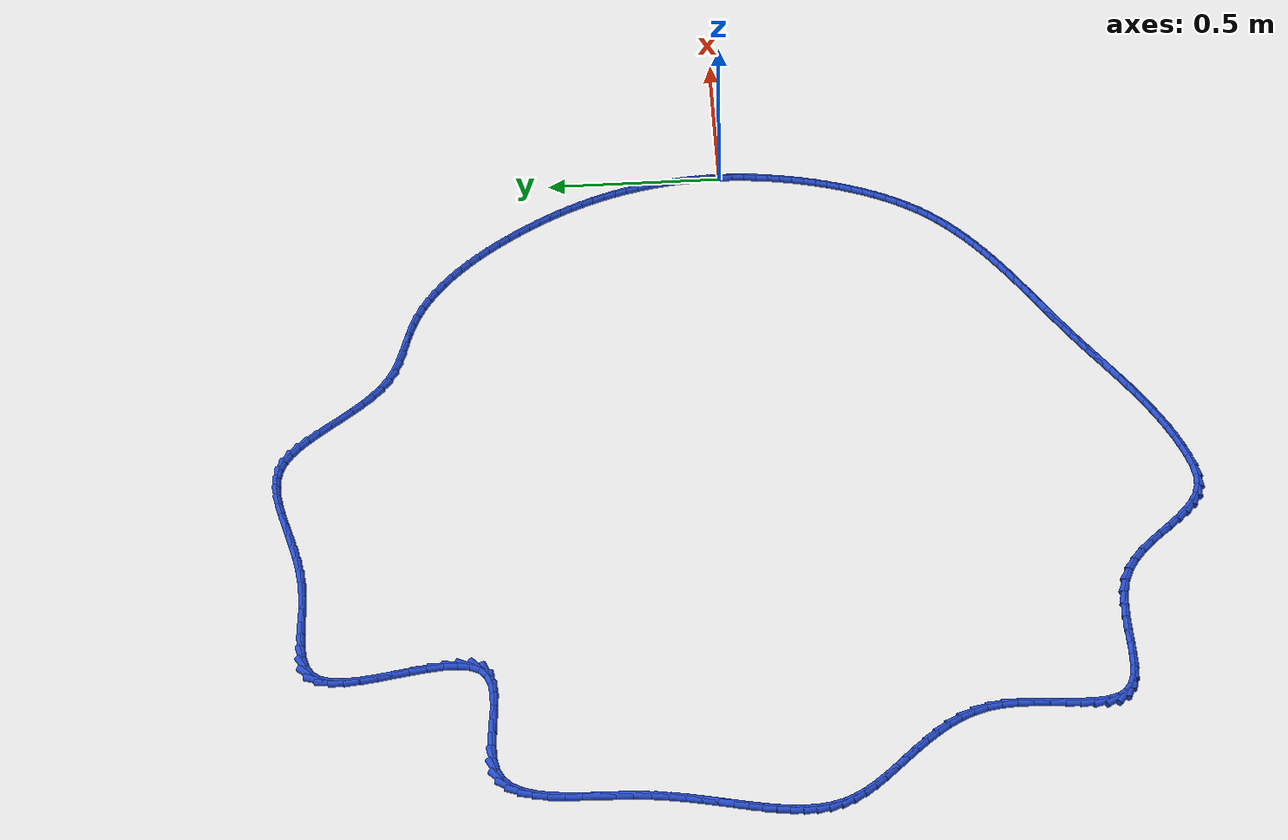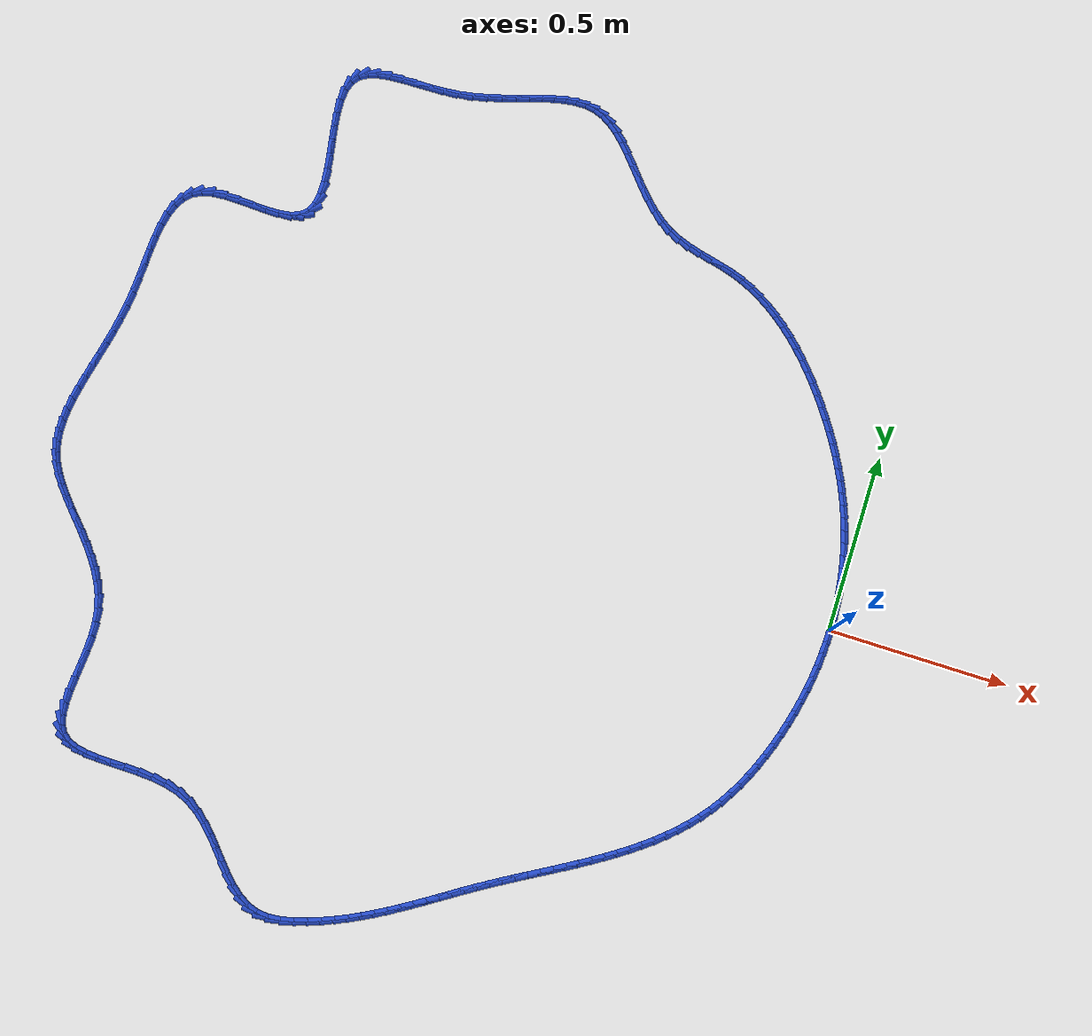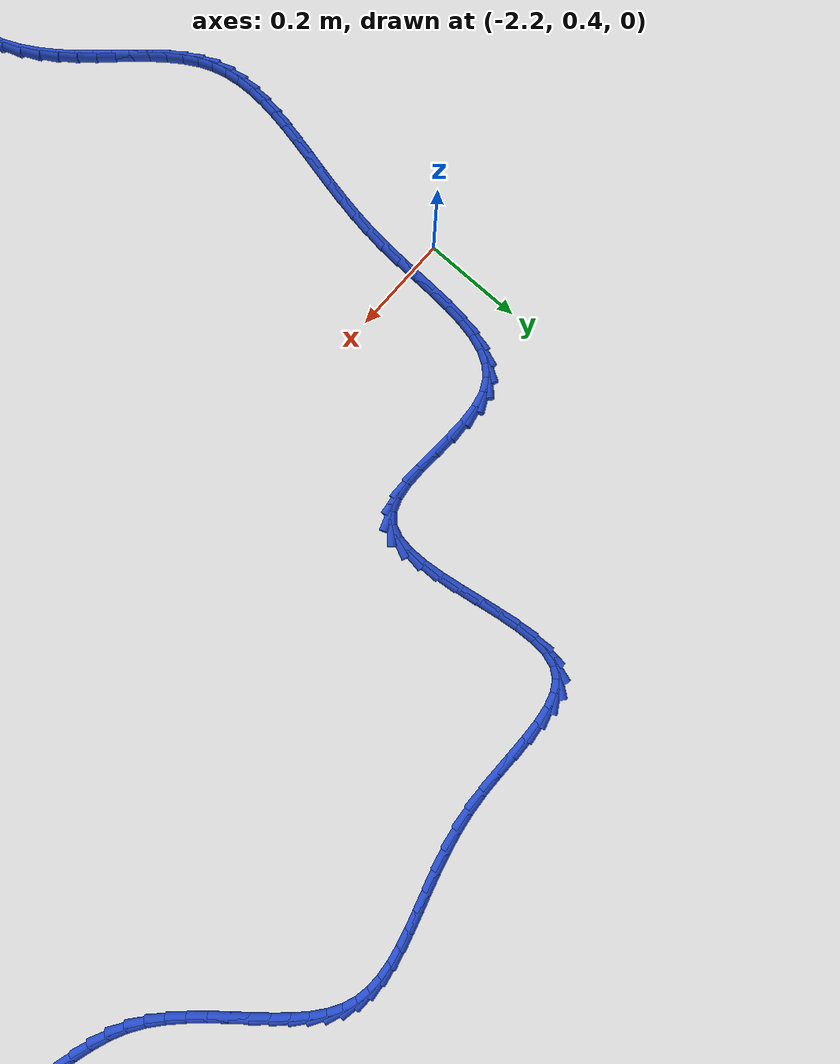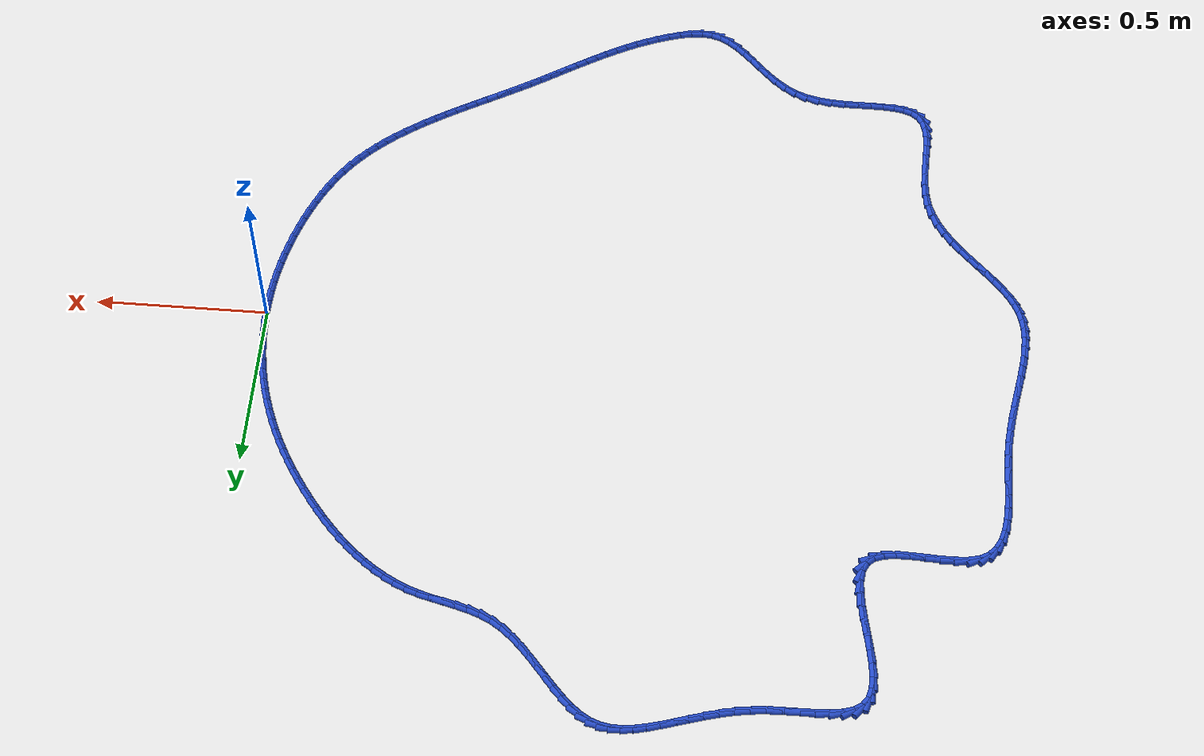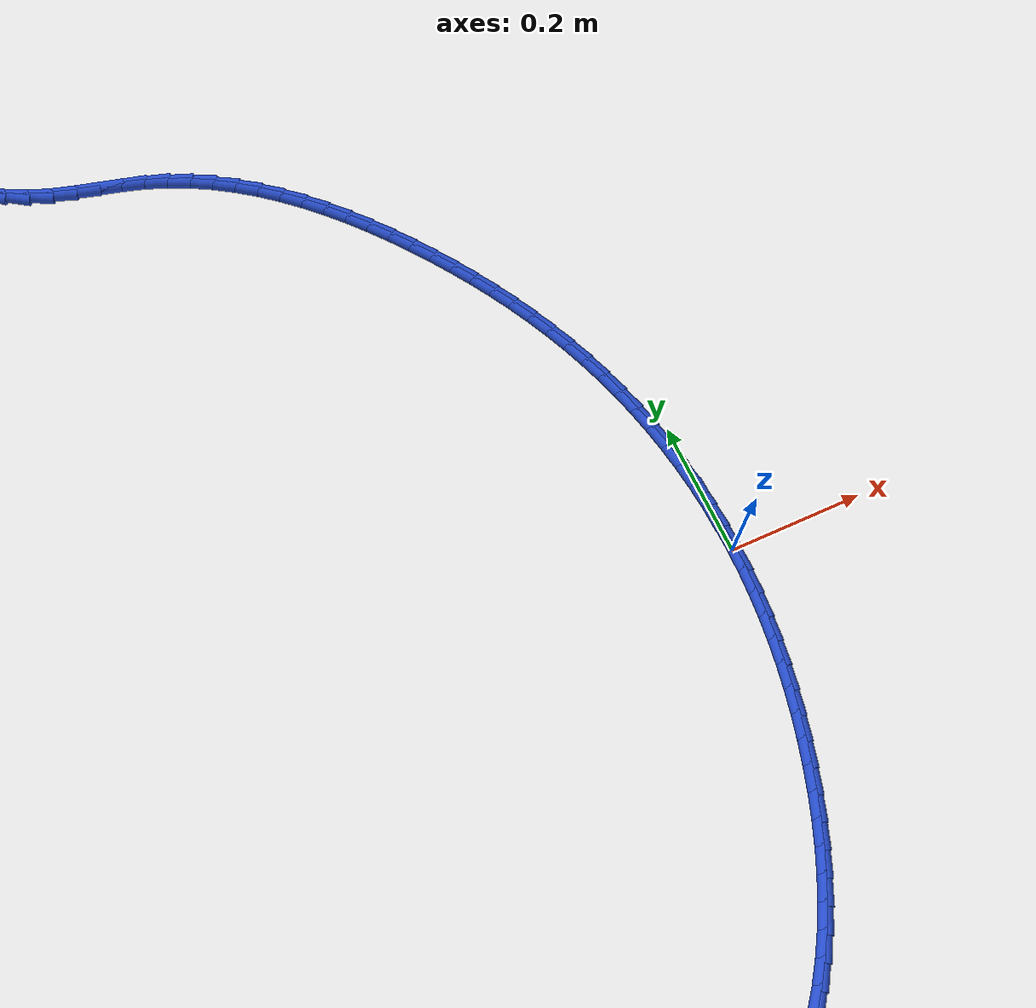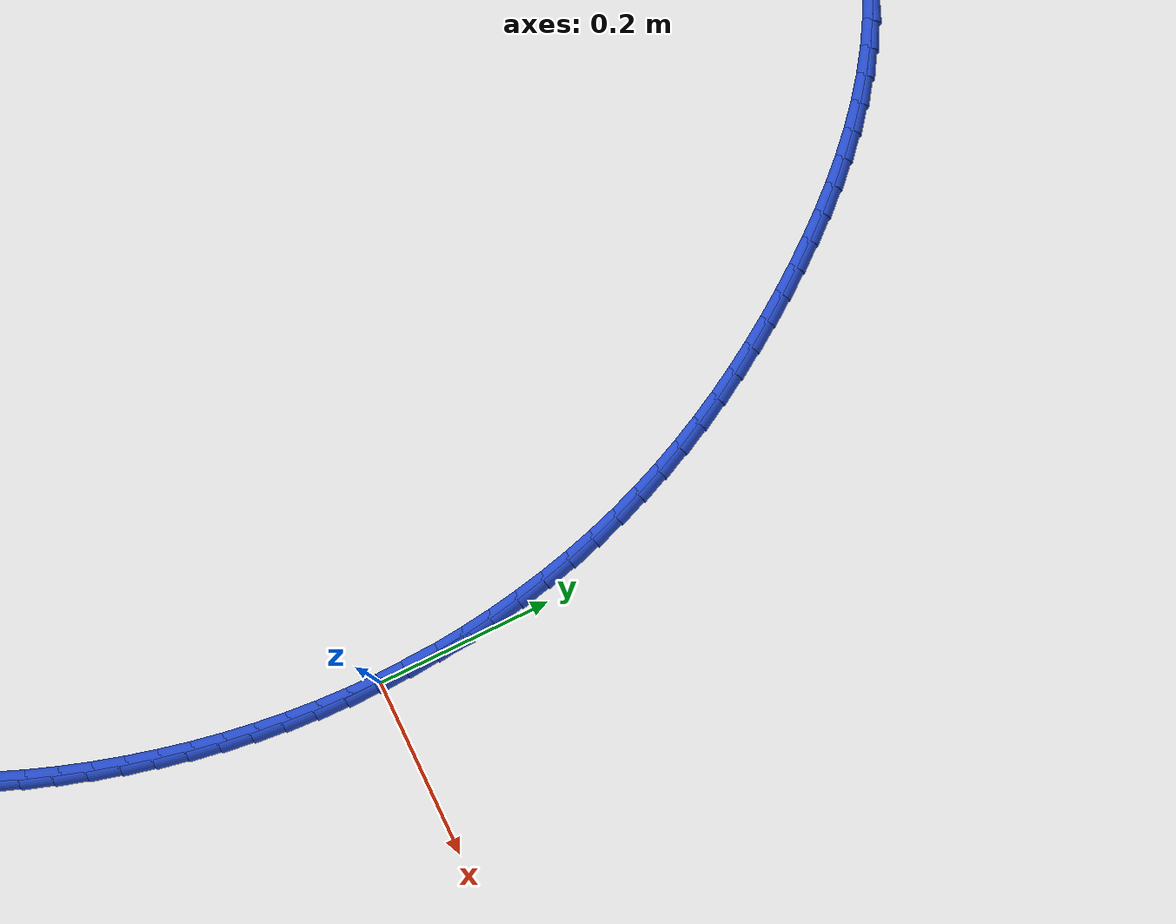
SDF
<sdf version="1.6">
 <world name="default">
  <light name="sun" type="directional">
   <pose>0 0 10 0 -0 0</pose>
   <diffuse>0.8 0.8 0.8 1</diffuse>
   <specular>0.2 0.2 0.2 1</specular>
   <attenuation>
    <range>1000</range>
    <constant>0.9</constant>
    <linear>0.01</linear>
    <quadratic>0.001</quadratic>
   </attenuation>
   <direction>-0.5 0.1 -0.9</direction>
  </light>
  <model name="ground_plane">
   <static>1</static>
   <link name="link">
    <collision name="collision">
     <geometry><plane><normal>0 0 1</normal><size>100 100</size></plane></geometry>
     <surface><friction><ode><mu>100</mu><mu2>50</mu2></ode></friction></surface>
    </collision>
    <visual name="visual">
     <cast_shadows>0</cast_shadows>
     <geometry><plane><normal>0 0 1</normal><size>100 100</size></plane></geometry>
     <material>
      <script><uri>file://media/materials/scripts/gazebo.material</uri><name>Gazebo/WhiteGlow</name></script>
     </material>
    </visual>
   </link>
  </model>
  <gravity>0 0 -9.8</gravity>
  <magnetic_field>6e-06 2.3e-05 -4.2e-05</magnetic_field>
  <atmosphere type="adiabatic"/>
  <physics name="default_physics" default="0" type="ode">
   <max_step_size>0.001</max_step_size>
   <real_time_factor>1</real_time_factor>
   <real_time_update_rate>1000</real_time_update_rate>
  </physics>
  <scene><ambient>0.4 0.4 0.4 1</ambient><background>0.7 0.7 0.7 1</background><shadows>1</shadows></scene>
  <spherical_coordinates>
   <surface_model>EARTH_WGS84</surface_model>
   <latitude_deg>0</latitude_deg>
   <longitude_deg>0</longitude_deg>
   <elevation>0</elevation>
   <heading_deg>0</heading_deg>
  </spherical_coordinates>
  <model name="line">
   <link name="link_0">
    <pose>-5.204170427930421e-18 -6.245004513516506e-17 0.01 0 1.57 -1.5561447790093017</pose>
    <collision name="collision">
     <geometry><cylinder><radius>0.01</radius><length>0.08</length></cylinder></geometry>
    </collision>
    <visual name="visual">
     <material>
      <script><name>Gazebo/Blue</name><uri>file://media/materials/scripts/gazebo.material</uri></script>
     </material>
     <geometry><cylinder><radius>0.01</radius><length>0.08</length></cylinder></geometry>
    </visual>
   </link>
   <link name="link_1">
    <pose>-0.0005162711267056635 0.03523410573817638 0.01 0 1.57 -1.5201662241441394</pose>
    <collision name="collision">
     <geometry><cylinder><radius>0.01</radius><length>0.08</length></cylinder></geometry>
    </collision>
    <visual name="visual">
     <material>
      <script><name>Gazebo/Blue</name><uri>file://media/materials/scripts/gazebo.material</uri></script>
     </material>
     <geometry><cylinder><radius>0.01</radius><length>0.08</length></cylinder></geometry>
    </visual>
   </link>
   <link name="link_2">
    <pose>-0.0023020913173392257 0.07047586722419166 0.01 0 1.57 -1.484297227940387</pose>
    <collision name="collision">
     <geometry><cylinder><radius>0.01</radius><length>0.08</length></cylinder></geometry>
    </collision>
    <visual name="visual">
     <material>
      <script><name>Gazebo/Blue</name><uri>file://media/materials/scripts/gazebo.material</uri></script>
     </material>
     <geometry><cylinder><radius>0.01</radius><length>0.08</length></cylinder></geometry>
    </visual>
   </link>
   <link name="link_3">
    <pose>-0.005352982997565068 0.10565864834959819 0.01 0 1.57 -1.4484263781673588</pose>
    <collision name="collision">
     <geometry><cylinder><radius>0.01</radius><length>0.08</length></cylinder></geometry>
    </collision>
    <visual name="visual">
     <material>
      <script><name>Gazebo/Blue</name><uri>file://media/materials/scripts/gazebo.material</uri></script>
     </material>
     <geometry><cylinder><radius>0.01</radius><length>0.08</length></cylinder></geometry>
    </visual>
   </link>
   <link name="link_4">
    <pose>-0.009664468593047574 0.14071581300594832 0.01 0 1.57 -1.4124426665159606</pose>
    <collision name="collision">
     <geometry><cylinder><radius>0.01</radius><length>0.08</length></cylinder></geometry>
    </collision>
    <visual name="visual">
     <material>
      <script><name>Gazebo/Blue</name><uri>file://media/materials/scripts/gazebo.material</uri></script>
     </material>
     <geometry><cylinder><radius>0.01</radius><length>0.08</length></cylinder></geometry>
    </visual>
   </link>
   <link name="link_5">
    <pose>-0.015232070529451134 0.17558072508479447 0.01 0 1.57 -1.3762354643773935</pose>
    <collision name="collision">
     <geometry><cylinder><radius>0.01</radius><length>0.08</length></cylinder></geometry>
    </collision>
    <visual name="visual">
     <material>
      <script><name>Gazebo/Blue</name><uri>file://media/materials/scripts/gazebo.material</uri></script>
     </material>
     <geometry><cylinder><radius>0.01</radius><length>0.08</length></cylinder></geometry>
    </visual>
   </link>
   <link name="link_6">
    <pose>-0.022051311232440127 0.21018674847768903 0.01 0 1.57 -1.3396945418003954</pose>
    <collision name="collision">
     <geometry><cylinder><radius>0.01</radius><length>0.08</length></cylinder></geometry>
    </collision>
    <visual name="visual">
     <material>
      <script><name>Gazebo/Blue</name><uri>file://media/materials/scripts/gazebo.material</uri></script>
     </material>
     <geometry><cylinder><radius>0.01</radius><length>0.08</length></cylinder></geometry>
    </visual>
   </link>
   <link name="link_7">
    <pose>-0.030117713127678938 0.24446724707618445 0.01 0 1.57 -1.3027101657882285</pose>
    <collision name="collision">
     <geometry><cylinder><radius>0.01</radius><length>0.08</length></cylinder></geometry>
    </collision>
    <visual name="visual">
     <material>
      <script><name>Gazebo/Blue</name><uri>file://media/materials/scripts/gazebo.material</uri></script>
     </material>
     <geometry><cylinder><radius>0.01</radius><length>0.08</length></cylinder></geometry>
    </visual>
   </link>
   <link name="link_8">
    <pose>-0.03942679864083194 0.2783555847718331 0.01 0 1.57 -1.2652072793712814</pose>
    <collision name="collision">
     <geometry><cylinder><radius>0.01</radius><length>0.08</length></cylinder></geometry>
    </collision>
    <visual name="visual">
     <material>
      <script><name>Gazebo/Blue</name><uri>file://media/materials/scripts/gazebo.material</uri></script>
     </material>
     <geometry><cylinder><radius>0.01</radius><length>0.08</length></cylinder></geometry>
    </visual>
   </link>
   <link name="link_9">
    <pose>-0.04997340024318076 0.31178689562437656 0.01 0 1.57 -1.2278604827539903</pose>
    <collision name="collision">
     <geometry><cylinder><radius>0.01</radius><length>0.08</length></cylinder></geometry>
    </collision>
    <visual name="visual">
     <material>
      <script><name>Gazebo/Blue</name><uri>file://media/materials/scripts/gazebo.material</uri></script>
     </material>
     <geometry><cylinder><radius>0.01</radius><length>0.08</length></cylinder></geometry>
    </visual>
   </link>
   <link name="link_10">
    <pose>-0.061737290473816424 0.34473495191886827 0.01 0 1.57 -1.1914613746429972</pose>
    <collision name="collision">
     <geometry><cylinder><radius>0.01</radius><length>0.08</length></cylinder></geometry>
    </collision>
    <visual name="visual">
     <material>
      <script><name>Gazebo/Blue</name><uri>file://media/materials/scripts/gazebo.material</uri></script>
     </material>
     <geometry><cylinder><radius>0.01</radius><length>0.08</length></cylinder></geometry>
    </visual>
   </link>
   <link name="link_11">
    <pose>-0.07468361813707979 0.3772110450441017 0.01 0 1.57 -1.1561365020602024</pose>
    <collision name="collision">
     <geometry><cylinder><radius>0.01</radius><length>0.08</length></cylinder></geometry>
    </collision>
    <visual name="visual">
     <material>
      <script><name>Gazebo/Blue</name><uri>file://media/materials/scripts/gazebo.material</uri></script>
     </material>
     <geometry><cylinder><radius>0.01</radius><length>0.08</length></cylinder></geometry>
    </visual>
   </link>
   <link name="link_12">
    <pose>-0.088776929346043 0.40922801267212894 0.01 0 1.57 -1.1219664509776546</pose>
    <collision name="collision">
     <geometry><cylinder><radius>0.01</radius><length>0.08</length></cylinder></geometry>
    </collision>
    <visual name="visual">
     <material>
      <script><name>Gazebo/Blue</name><uri>file://media/materials/scripts/gazebo.material</uri></script>
     </material>
     <geometry><cylinder><radius>0.01</radius><length>0.08</length></cylinder></geometry>
    </visual>
   </link>
   <link name="link_13">
    <pose>-0.10398177021377833 0.4407986924750029 0.01 0 1.57 -1.0890156814608125</pose>
    <collision name="collision">
     <geometry><cylinder><radius>0.01</radius><length>0.08</length></cylinder></geometry>
    </collision>
    <visual name="visual">
     <material>
      <script><name>Gazebo/Blue</name><uri>file://media/materials/scripts/gazebo.material</uri></script>
     </material>
     <geometry><cylinder><radius>0.01</radius><length>0.08</length></cylinder></geometry>
    </visual>
   </link>
   <link name="link_14">
    <pose>-0.12026268685335802 0.47193592212477603 0.01 0 1.57 -1.0573331796554482</pose>
    <collision name="collision">
     <geometry><cylinder><radius>0.01</radius><length>0.08</length></cylinder></geometry>
    </collision>
    <visual name="visual">
     <material>
      <script><name>Gazebo/Blue</name><uri>file://media/materials/scripts/gazebo.material</uri></script>
     </material>
     <geometry><cylinder><radius>0.01</radius><length>0.08</length></cylinder></geometry>
    </visual>
   </link>
   <link name="link_15">
    <pose>-0.1375842253778542 0.5026525392935007 0.01 0 1.57 -1.0269534876532893</pose>
    <collision name="collision">
     <geometry><cylinder><radius>0.01</radius><length>0.08</length></cylinder></geometry>
    </collision>
    <visual name="visual">
     <material>
      <script><name>Gazebo/Blue</name><uri>file://media/materials/scripts/gazebo.material</uri></script>
     </material>
     <geometry><cylinder><radius>0.01</radius><length>0.08</length></cylinder></geometry>
    </visual>
   </link>
   <link name="link_16">
    <pose>-0.1559109319003392 0.5329613816532298 0.01 0 1.57 -0.9978980035696883</pose>
    <collision name="collision">
     <geometry><cylinder><radius>0.01</radius><length>0.08</length></cylinder></geometry>
    </collision>
    <visual name="visual">
     <material>
      <script><name>Gazebo/Blue</name><uri>file://media/materials/scripts/gazebo.material</uri></script>
     </material>
     <geometry><cylinder><radius>0.01</radius><length>0.08</length></cylinder></geometry>
    </visual>
   </link>
   <link name="link_17">
    <pose>-0.17520735253388506 0.5628752868760153 0.01 0 1.57 -0.9701764500124382</pose>
    <collision name="collision">
     <geometry><cylinder><radius>0.01</radius><length>0.08</length></cylinder></geometry>
    </collision>
    <visual name="visual">
     <material>
      <script><name>Gazebo/Blue</name><uri>file://media/materials/scripts/gazebo.material</uri></script>
     </material>
     <geometry><cylinder><radius>0.01</radius><length>0.08</length></cylinder></geometry>
    </visual>
   </link>
   <link name="link_18">
    <pose>-0.19543803339156413 0.59240709263391 0.01 0 1.57 -0.9436973816188705</pose>
    <collision name="collision">
     <geometry><cylinder><radius>0.01</radius><length>0.08</length></cylinder></geometry>
    </collision>
    <visual name="visual">
     <material>
      <script><name>Gazebo/Blue</name><uri>file://media/materials/scripts/gazebo.material</uri></script>
     </material>
     <geometry><cylinder><radius>0.01</radius><length>0.08</length></cylinder></geometry>
    </visual>
   </link>
   <link name="link_19">
    <pose>-0.21656862724549292 0.6215655764697207 0.01 0 1.57 -0.9163910836548914</pose>
    <collision name="collision">
     <geometry><cylinder><radius>0.01</radius><length>0.08</length></cylinder></geometry>
    </collision>
    <visual name="visual">
     <material>
      <script><name>Gazebo/Blue</name><uri>file://media/materials/scripts/gazebo.material</uri></script>
     </material>
     <geometry><cylinder><radius>0.01</radius><length>0.08</length></cylinder></geometry>
    </visual>
   </link>
   <link name="link_20">
    <pose>-0.2385894137453627 0.6502691644251356 0.01 0 1.57 -0.8860877698987994</pose>
    <collision name="collision">
     <geometry><cylinder><radius>0.01</radius><length>0.08</length></cylinder></geometry>
    </collision>
    <visual name="visual">
     <material>
      <script><name>Gazebo/Blue</name><uri>file://media/materials/scripts/gazebo.material</uri></script>
     </material>
     <geometry><cylinder><radius>0.01</radius><length>0.08</length></cylinder></geometry>
    </visual>
   </link>
   <link name="link_21">
    <pose>-0.26151484893691174 0.678347583774905 0.01 0 1.57 -0.8524603840495918</pose>
    <collision name="collision">
     <geometry><cylinder><radius>0.01</radius><length>0.08</length></cylinder></geometry>
    </collision>
    <visual name="visual">
     <material>
      <script><name>Gazebo/Blue</name><uri>file://media/materials/scripts/gazebo.material</uri></script>
     </material>
     <geometry><cylinder><radius>0.01</radius><length>0.08</length></cylinder></geometry>
    </visual>
   </link>
   <link name="link_22">
    <pose>-0.2853604054189903 0.7056268322466858 0.01 0 1.57 -0.8152387404536157</pose>
    <collision name="collision">
     <geometry><cylinder><radius>0.01</radius><length>0.08</length></cylinder></geometry>
    </collision>
    <visual name="visual">
     <material>
      <script><name>Gazebo/Blue</name><uri>file://media/materials/scripts/gazebo.material</uri></script>
     </material>
     <geometry><cylinder><radius>0.01</radius><length>0.08</length></cylinder></geometry>
    </visual>
   </link>
   <link name="link_23">
    <pose>-0.3101415557904487 0.7319329075681348 0.01 0 1.57 -0.774133079321631</pose>
    <collision name="collision">
     <geometry><cylinder><radius>0.01</radius><length>0.08</length></cylinder></geometry>
    </collision>
    <visual name="visual">
     <material>
      <script><name>Gazebo/Blue</name><uri>file://media/materials/scripts/gazebo.material</uri></script>
     </material>
     <geometry><cylinder><radius>0.01</radius><length>0.08</length></cylinder></geometry>
    </visual>
   </link>
   <link name="link_24">
    <pose>-0.3358737726501376 0.7570918074669097 0.01 0 1.57 -0.7288452907351434</pose>
    <collision name="collision">
     <geometry><cylinder><radius>0.01</radius><length>0.08</length></cylinder></geometry>
    </collision>
    <visual name="visual">
     <material>
      <script><name>Gazebo/Blue</name><uri>file://media/materials/scripts/gazebo.material</uri></script>
     </material>
     <geometry><cylinder><radius>0.01</radius><length>0.08</length></cylinder></geometry>
    </visual>
   </link>
   <link name="link_25">
    <pose>-0.362572528596907 0.7809295296706673 0.01 0 1.57 -0.6790857506434033</pose>
    <collision name="collision">
     <geometry><cylinder><radius>0.01</radius><length>0.08</length></cylinder></geometry>
    </collision>
    <visual name="visual">
     <material>
      <script><name>Gazebo/Blue</name><uri>file://media/materials/scripts/gazebo.material</uri></script>
     </material>
     <geometry><cylinder><radius>0.01</radius><length>0.08</length></cylinder></geometry>
    </visual>
   </link>
   <link name="link_26">
    <pose>-0.39025329622960775 0.8032720719070652 0.01 0 1.57 -0.6245973608186239</pose>
    <collision name="collision">
     <geometry><cylinder><radius>0.01</radius><length>0.08</length></cylinder></geometry>
    </collision>
    <visual name="visual">
     <material>
      <script><name>Gazebo/Blue</name><uri>file://media/materials/scripts/gazebo.material</uri></script>
     </material>
     <geometry><cylinder><radius>0.01</radius><length>0.08</length></cylinder></geometry>
    </visual>
   </link>
   <link name="link_27">
    <pose>-0.41893154814709 0.8239454319037602 0.01 0 1.57 -0.5651879689845339</pose>
    <collision name="collision">
     <geometry><cylinder><radius>0.01</radius><length>0.08</length></cylinder></geometry>
    </collision>
    <visual name="visual">
     <material>
      <script><name>Gazebo/Blue</name><uri>file://media/materials/scripts/gazebo.material</uri></script>
     </material>
     <geometry><cylinder><radius>0.01</radius><length>0.08</length></cylinder></geometry>
    </visual>
   </link>
   <link name="link_28">
    <pose>-0.44862275694820414 0.8427756073884094 0.01 0 1.57 -0.5007711842867857</pose>
    <collision name="collision">
     <geometry><cylinder><radius>0.01</radius><length>0.08</length></cylinder></geometry>
    </collision>
    <visual name="visual">
     <material>
      <script><name>Gazebo/Blue</name><uri>file://media/materials/scripts/gazebo.material</uri></script>
     </material>
     <geometry><cylinder><radius>0.01</radius><length>0.08</length></cylinder></geometry>
    </visual>
   </link>
   <link name="link_29">
    <pose>-0.4793423952318004 0.8595885960886702 0.01 0 1.57 -0.4314133885231121</pose>
    <collision name="collision">
     <geometry><cylinder><radius>0.01</radius><length>0.08</length></cylinder></geometry>
    </collision>
    <visual name="visual">
     <material>
      <script><name>Gazebo/Blue</name><uri>file://media/materials/scripts/gazebo.material</uri></script>
     </material>
     <geometry><cylinder><radius>0.01</radius><length>0.08</length></cylinder></geometry>
    </visual>
   </link>
   <link name="link_30">
    <pose>-0.5111059355967295 0.8742103957321994 0.01 0 1.57 -0.35740596119619195</pose>
    <collision name="collision">
     <geometry><cylinder><radius>0.01</radius><length>0.08</length></cylinder></geometry>
    </collision>
    <visual name="visual">
     <material>
      <script><name>Gazebo/Blue</name><uri>file://media/materials/scripts/gazebo.material</uri></script>
     </material>
     <geometry><cylinder><radius>0.01</radius><length>0.08</length></cylinder></geometry>
    </visual>
   </link>
   <link name="link_31">
    <pose>-0.543928541942957 0.8864678068465407 0.01 0 1.57 -0.28927580626145466</pose>
    <collision name="collision">
     <geometry><cylinder><radius>0.01</radius><length>0.08</length></cylinder></geometry>
    </collision>
    <visual name="visual">
     <material>
      <script><name>Gazebo/Blue</name><uri>file://media/materials/scripts/gazebo.material</uri></script>
     </material>
     <geometry><cylinder><radius>0.01</radius><length>0.08</length></cylinder></geometry>
    </visual>
   </link>
   <link name="link_32">
    <pose>-0.5776981626372233 0.8965184656722677 0.01 0 1.57 -0.25238562214267</pose>
    <collision name="collision">
     <geometry><cylinder><radius>0.01</radius><length>0.08</length></cylinder></geometry>
    </collision>
    <visual name="visual">
     <material>
      <script><name>Gazebo/Blue</name><uri>file://media/materials/scripts/gazebo.material</uri></script>
     </material>
     <geometry><cylinder><radius>0.01</radius><length>0.08</length></cylinder></geometry>
    </visual>
   </link>
   <link name="link_33">
    <pose>-0.6119800400102237 0.9053592352238206 0.01 0 1.57 -0.2499535344653592</pose>
    <collision name="collision">
     <geometry><cylinder><radius>0.01</radius><length>0.08</length></cylinder></geometry>
    </collision>
    <visual name="visual">
     <material>
      <script><name>Gazebo/Blue</name><uri>file://media/materials/scripts/gazebo.material</uri></script>
     </material>
     <geometry><cylinder><radius>0.01</radius><length>0.08</length></cylinder></geometry>
    </visual>
   </link>
   <link name="link_34">
    <pose>-0.6462890133444913 0.914118056285425 0.01 0 1.57 -0.2819317547828635</pose>
    <collision name="collision">
     <geometry><cylinder><radius>0.01</radius><length>0.08</length></cylinder></geometry>
    </collision>
    <visual name="visual">
     <material>
      <script><name>Gazebo/Blue</name><uri>file://media/materials/scripts/gazebo.material</uri></script>
     </material>
     <geometry><cylinder><radius>0.01</radius><length>0.08</length></cylinder></geometry>
    </visual>
   </link>
   <link name="link_35">
    <pose>-0.6801399219225605 0.9239228696413063 0.01 0 1.57 -0.3491015196145687</pose>
    <collision name="collision">
     <geometry><cylinder><radius>0.01</radius><length>0.08</length></cylinder></geometry>
    </collision>
    <visual name="visual">
     <material>
      <script><name>Gazebo/Blue</name><uri>file://media/materials/scripts/gazebo.material</uri></script>
     </material>
     <geometry><cylinder><radius>0.01</radius><length>0.08</length></cylinder></geometry>
    </visual>
   </link>
   <link name="link_36">
    <pose>-0.7130476050269647 0.9359016160756902 0.01 0 1.57 -0.451914180970877</pose>
    <collision name="collision">
     <geometry><cylinder><radius>0.01</radius><length>0.08</length></cylinder></geometry>
    </collision>
    <visual name="visual">
     <material>
      <script><name>Gazebo/Blue</name><uri>file://media/materials/scripts/gazebo.material</uri></script>
     </material>
     <geometry><cylinder><radius>0.01</radius><length>0.08</length></cylinder></geometry>
    </visual>
   </link>
   <link name="link_37">
    <pose>-0.7445269019402381 0.9511822363728022 0.01 0 1.57 -0.5812640832778858</pose>
    <collision name="collision">
     <geometry><cylinder><radius>0.01</radius><length>0.08</length></cylinder></geometry>
    </collision>
    <visual name="visual">
     <material>
      <script><name>Gazebo/Blue</name><uri>file://media/materials/scripts/gazebo.material</uri></script>
     </material>
     <geometry><cylinder><radius>0.01</radius><length>0.08</length></cylinder></geometry>
    </visual>
   </link>
   <link name="link_38">
    <pose>-0.7741799042986441 0.9706635660153689 0.01 0 1.57 -0.6939139569976287</pose>
    <collision name="collision">
     <geometry><cylinder><radius>0.01</radius><length>0.08</length></cylinder></geometry>
    </collision>
    <visual name="visual">
     <material>
      <script><name>Gazebo/Blue</name><uri>file://media/materials/scripts/gazebo.material</uri></script>
     </material>
     <geometry><cylinder><radius>0.01</radius><length>0.08</length></cylinder></geometry>
    </visual>
   </link>
   <link name="link_39">
    <pose>-0.8021182386866487 0.9939065148836177 0.01 0 1.57 -0.7770614135203776</pose>
    <collision name="collision">
     <geometry><cylinder><radius>0.01</radius><length>0.08</length></cylinder></geometry>
    </collision>
    <visual name="visual">
     <material>
      <script><name>Gazebo/Blue</name><uri>file://media/materials/scripts/gazebo.material</uri></script>
     </material>
     <geometry><cylinder><radius>0.01</radius><length>0.08</length></cylinder></geometry>
    </visual>
   </link>
   <link name="link_40">
    <pose>-0.8286379654534977 1.0199877107555733 0.01 0 1.57 -0.8340174433594522</pose>
    <collision name="collision">
     <geometry><cylinder><radius>0.01</radius><length>0.08</length></cylinder></geometry>
    </collision>
    <visual name="visual">
     <material>
      <script><name>Gazebo/Blue</name><uri>file://media/materials/scripts/gazebo.material</uri></script>
     </material>
     <geometry><cylinder><radius>0.01</radius><length>0.08</length></cylinder></geometry>
    </visual>
   </link>
   <link name="link_41">
    <pose>-0.8540353993806037 1.047983113326898 0.01 0 1.57 -0.8676312374345876</pose>
    <collision name="collision">
     <geometry><cylinder><radius>0.01</radius><length>0.08</length></cylinder></geometry>
    </collision>
    <visual name="visual">
     <material>
      <script><name>Gazebo/Blue</name><uri>file://media/materials/scripts/gazebo.material</uri></script>
     </material>
     <geometry><cylinder><radius>0.01</radius><length>0.08</length></cylinder></geometry>
    </visual>
   </link>
   <link name="link_42">
    <pose>-0.8786068552493808 1.0769686822932543 0.01 0 1.57 -0.8794796137078563</pose>
    <collision name="collision">
     <geometry><cylinder><radius>0.01</radius><length>0.08</length></cylinder></geometry>
    </collision>
    <visual name="visual">
     <material>
      <script><name>Gazebo/Blue</name><uri>file://media/materials/scripts/gazebo.material</uri></script>
     </material>
     <geometry><cylinder><radius>0.01</radius><length>0.08</length></cylinder></geometry>
    </visual>
   </link>
   <link name="link_43">
    <pose>-0.9026486478412412 1.1060203773503043 0.01 0 1.57 -0.8695288986471125</pose>
    <collision name="collision">
     <geometry><cylinder><radius>0.01</radius><length>0.08</length></cylinder></geometry>
    </collision>
    <visual name="visual">
     <material>
      <script><name>Gazebo/Blue</name><uri>file://media/materials/scripts/gazebo.material</uri></script>
     </material>
     <geometry><cylinder><radius>0.01</radius><length>0.08</length></cylinder></geometry>
    </visual>
   </link>
   <link name="link_44">
    <pose>-0.9264570919375988 1.1342141581937109 0.01 0 1.57 -0.8358773679130423</pose>
    <collision name="collision">
     <geometry><cylinder><radius>0.01</radius><length>0.08</length></cylinder></geometry>
    </collision>
    <visual name="visual">
     <material>
      <script><name>Gazebo/Blue</name><uri>file://media/materials/scripts/gazebo.material</uri></script>
     </material>
     <geometry><cylinder><radius>0.01</radius><length>0.08</length></cylinder></geometry>
    </visual>
   </link>
   <link name="link_45">
    <pose>-0.9503285023198667 1.1606259845191358 0.01 0 1.57 -0.774449539218626</pose>
    <collision name="collision">
     <geometry><cylinder><radius>0.01</radius><length>0.08</length></cylinder></geometry>
    </collision>
    <visual name="visual">
     <material>
      <script><name>Gazebo/Blue</name><uri>file://media/materials/scripts/gazebo.material</uri></script>
     </material>
     <geometry><cylinder><radius>0.01</radius><length>0.08</length></cylinder></geometry>
    </visual>
   </link>
   <link name="link_46">
    <pose>-0.9745591937694579 1.184331816022242 0.01 0 1.57 -0.6788136685192349</pose>
    <collision name="collision">
     <geometry><cylinder><radius>0.01</radius><length>0.08</length></cylinder></geometry>
    </collision>
    <visual name="visual">
     <material>
      <script><name>Gazebo/Blue</name><uri>file://media/materials/scripts/gazebo.material</uri></script>
     </material>
     <geometry><cylinder><radius>0.01</radius><length>0.08</length></cylinder></geometry>
    </visual>
   </link>
   <link name="link_47">
    <pose>-0.9994454810677855 1.204407612398692 0.01 0 1.57 -0.540954394392659</pose>
    <collision name="collision">
     <geometry><cylinder><radius>0.01</radius><length>0.08</length></cylinder></geometry>
    </collision>
    <visual name="visual">
     <material>
      <script><name>Gazebo/Blue</name><uri>file://media/materials/scripts/gazebo.material</uri></script>
     </material>
     <geometry><cylinder><radius>0.01</radius><length>0.08</length></cylinder></geometry>
    </visual>
   </link>
   <link name="link_48">
    <pose>-1.0252836789962636 1.2199293333441479 0.01 0 1.57 -0.35797915116455686</pose>
    <collision name="collision">
     <geometry><cylinder><radius>0.01</radius><length>0.08</length></cylinder></geometry>
    </collision>
    <visual name="visual">
     <material>
      <script><name>Gazebo/Blue</name><uri>file://media/materials/scripts/gazebo.material</uri></script>
     </material>
     <geometry><cylinder><radius>0.01</radius><length>0.08</length></cylinder></geometry>
    </visual>
   </link>
   <link name="link_49">
    <pose>-1.052354672991753 1.23005652292937 0.01 0 1.57 -0.16926272702374756</pose>
    <collision name="collision">
     <geometry><cylinder><radius>0.01</radius><length>0.08</length></cylinder></geometry>
    </collision>
    <visual name="visual">
     <material>
      <script><name>Gazebo/Blue</name><uri>file://media/materials/scripts/gazebo.material</uri></script>
     </material>
     <geometry><cylinder><radius>0.01</radius><length>0.08</length></cylinder></geometry>
    </visual>
   </link>
   <link name="link_50">
    <pose>-1.0807616756549256 1.2349112206140833 0.01 0 1.57 -0.010791913638561466</pose>
    <collision name="collision">
     <geometry><cylinder><radius>0.01</radius><length>0.08</length></cylinder></geometry>
    </collision>
    <visual name="visual">
     <material>
      <script><name>Gazebo/Blue</name><uri>file://media/materials/scripts/gazebo.material</uri></script>
     </material>
     <geometry><cylinder><radius>0.01</radius><length>0.08</length></cylinder></geometry>
    </visual>
   </link>
   <link name="link_51">
    <pose>-1.1104940709025146 1.2352321025131725 0.01 0 1.57 0.11112474251257212</pose>
    <collision name="collision">
     <geometry><cylinder><radius>0.01</radius><length>0.08</length></cylinder></geometry>
    </collision>
    <visual name="visual">
     <material>
      <script><name>Gazebo/Blue</name><uri>file://media/materials/scripts/gazebo.material</uri></script>
     </material>
     <geometry><cylinder><radius>0.01</radius><length>0.08</length></cylinder></geometry>
    </visual>
   </link>
   <link name="link_52">
    <pose>-1.1415393810806551 1.2317679293056794 0.01 0 1.57 0.1983263772736202</pose>
    <collision name="collision">
     <geometry><cylinder><radius>0.01</radius><length>0.08</length></cylinder></geometry>
    </collision>
    <visual name="visual">
     <material>
      <script><name>Gazebo/Blue</name><uri>file://media/materials/scripts/gazebo.material</uri></script>
     </material>
     <geometry><cylinder><radius>0.01</radius><length>0.08</length></cylinder></geometry>
    </visual>
   </link>
   <link name="link_53">
    <pose>-1.1738851285354848 1.2252674616706463 0.01 0 1.57 0.25557182310923393</pose>
    <collision name="collision">
     <geometry><cylinder><radius>0.01</radius><length>0.08</length></cylinder></geometry>
    </collision>
    <visual name="visual">
     <material>
      <script><name>Gazebo/Blue</name><uri>file://media/materials/scripts/gazebo.material</uri></script>
     </material>
     <geometry><cylinder><radius>0.01</radius><length>0.08</length></cylinder></geometry>
    </visual>
   </link>
   <link name="link_54">
    <pose>-1.2075188356131386 1.2164794602871143 0.01 0 1.57 0.28761590483058164</pose>
    <collision name="collision">
     <geometry><cylinder><radius>0.01</radius><length>0.08</length></cylinder></geometry>
    </collision>
    <visual name="visual">
     <material>
      <script><name>Gazebo/Blue</name><uri>file://media/materials/scripts/gazebo.material</uri></script>
     </material>
     <geometry><cylinder><radius>0.01</radius><length>0.08</length></cylinder></geometry>
    </visual>
   </link>
   <link name="link_55">
    <pose>-1.2424280246597537 1.2061526858341252 0.01 0 1.57 0.2981675878896848</pose>
    <collision name="collision">
     <geometry><cylinder><radius>0.01</radius><length>0.08</length></cylinder></geometry>
    </collision>
    <visual name="visual">
     <material>
      <script><name>Gazebo/Blue</name><uri>file://media/materials/scripts/gazebo.material</uri></script>
     </material>
     <geometry><cylinder><radius>0.01</radius><length>0.08</length></cylinder></geometry>
    </visual>
   </link>
   <link name="link_56">
    <pose>-1.2786002180214664 1.1950358989907204 0.01 0 1.57 0.28976983924417815</pose>
    <collision name="collision">
     <geometry><cylinder><radius>0.01</radius><length>0.08</length></cylinder></geometry>
    </collision>
    <visual name="visual">
     <material>
      <script><name>Gazebo/Blue</name><uri>file://media/materials/scripts/gazebo.material</uri></script>
     </material>
     <geometry><cylinder><radius>0.01</radius><length>0.08</length></cylinder></geometry>
    </visual>
   </link>
   <link name="link_57">
    <pose>-1.3160229380444126 1.1838778604359421 0.01 0 1.57 0.26400405345316796</pose>
    <collision name="collision">
     <geometry><cylinder><radius>0.01</radius><length>0.08</length></cylinder></geometry>
    </collision>
    <visual name="visual">
     <material>
      <script><name>Gazebo/Blue</name><uri>file://media/materials/scripts/gazebo.material</uri></script>
     </material>
     <geometry><cylinder><radius>0.01</radius><length>0.08</length></cylinder></geometry>
    </visual>
   </link>
   <link name="link_58">
    <pose>-1.3546837070747286 1.1734273308488314 0.01 0 1.57 0.22178767855473136</pose>
    <collision name="collision">
     <geometry><cylinder><radius>0.01</radius><length>0.08</length></cylinder></geometry>
    </collision>
    <visual name="visual">
     <material>
      <script><name>Gazebo/Blue</name><uri>file://media/materials/scripts/gazebo.material</uri></script>
     </material>
     <geometry><cylinder><radius>0.01</radius><length>0.08</length></cylinder></geometry>
    </visual>
   </link>
   <link name="link_59">
    <pose>-1.394570047458551 1.1644330709084307 0.01 0 1.57 0.1637119114394083</pose>
    <collision name="collision">
     <geometry><cylinder><radius>0.01</radius><length>0.08</length></cylinder></geometry>
    </collision>
    <visual name="visual">
     <material>
      <script><name>Gazebo/Blue</name><uri>file://media/materials/scripts/gazebo.material</uri></script>
     </material>
     <geometry><cylinder><radius>0.01</radius><length>0.08</length></cylinder></geometry>
    </visual>
   </link>
   <link name="link_60">
    <pose>-1.4356694815420166 1.1576438412937808 0.01 0 1.57 0.09232077611445716</pose>
    <collision name="collision">
     <geometry><cylinder><radius>0.01</radius><length>0.08</length></cylinder></geometry>
    </collision>
    <visual name="visual">
     <material>
      <script><name>Gazebo/Blue</name><uri>file://media/materials/scripts/gazebo.material</uri></script>
     </material>
     <geometry><cylinder><radius>0.01</radius><length>0.08</length></cylinder></geometry>
    </visual>
   </link>
   <link name="link_61">
    <pose>-1.4779287514167638 1.1537313107164613 0.01 0 1.57 0.034576199099833886</pose>
    <collision name="collision">
     <geometry><cylinder><radius>0.01</radius><length>0.08</length></cylinder></geometry>
    </collision>
    <visual name="visual">
     <material>
      <script><name>Gazebo/Blue</name><uri>file://media/materials/scripts/gazebo.material</uri></script>
     </material>
     <geometry><cylinder><radius>0.01</radius><length>0.08</length></cylinder></geometry>
    </visual>
   </link>
   <link name="link_62">
    <pose>-1.5207045456765935 1.1522516966575977 0.01 0 1.57 0.007821012562774132</pose>
    <collision name="collision">
     <geometry><cylinder><radius>0.01</radius><length>0.08</length></cylinder></geometry>
    </collision>
    <visual name="visual">
     <material>
      <script><name>Gazebo/Blue</name><uri>file://media/materials/scripts/gazebo.material</uri></script>
     </material>
     <geometry><cylinder><radius>0.01</radius><length>0.08</length></cylinder></geometry>
    </visual>
   </link>
   <link name="link_63">
    <pose>-1.5629094136527377 1.1519216051245462 0.01 0 1.57 0.011951572840948698</pose>
    <collision name="collision">
     <geometry><cylinder><radius>0.01</radius><length>0.08</length></cylinder></geometry>
    </collision>
    <visual name="visual">
     <material>
      <script><name>Gazebo/Blue</name><uri>file://media/materials/scripts/gazebo.material</uri></script>
     </material>
     <geometry><cylinder><radius>0.01</radius><length>0.08</length></cylinder></geometry>
    </visual>
   </link>
   <link name="link_64">
    <pose>-1.603445047508792 1.1514371174755549 0.01 0 1.57 0.05139501109117642</pose>
    <collision name="collision">
     <geometry><cylinder><radius>0.01</radius><length>0.08</length></cylinder></geometry>
    </collision>
    <visual name="visual">
     <material>
      <script><name>Gazebo/Blue</name><uri>file://media/materials/scripts/gazebo.material</uri></script>
     </material>
     <geometry><cylinder><radius>0.01</radius><length>0.08</length></cylinder></geometry>
    </visual>
   </link>
   <link name="link_65">
    <pose>-1.6412131394083551 1.1494943150688741 0.01 0 1.57 0.13790158563755042</pose>
    <collision name="collision">
     <geometry><cylinder><radius>0.01</radius><length>0.08</length></cylinder></geometry>
    </collision>
    <visual name="visual">
     <material>
      <script><name>Gazebo/Blue</name><uri>file://media/materials/scripts/gazebo.material</uri></script>
     </material>
     <geometry><cylinder><radius>0.01</radius><length>0.08</length></cylinder></geometry>
    </visual>
   </link>
   <link name="link_66">
    <pose>-1.6751153815150246 1.1447892792627523 0.01 0 1.57 0.2943001220706854</pose>
    <collision name="collision">
     <geometry><cylinder><radius>0.01</radius><length>0.08</length></cylinder></geometry>
    </collision>
    <visual name="visual">
     <material>
      <script><name>Gazebo/Blue</name><uri>file://media/materials/scripts/gazebo.material</uri></script>
     </material>
     <geometry><cylinder><radius>0.01</radius><length>0.08</length></cylinder></geometry>
    </visual>
   </link>
   <link name="link_67">
    <pose>-1.7040534659923967 1.136018091415439 0.01 0 1.57 0.5536802714463099</pose>
    <collision name="collision">
     <geometry><cylinder><radius>0.01</radius><length>0.08</length></cylinder></geometry>
    </collision>
    <visual name="visual">
     <material>
      <script><name>Gazebo/Blue</name><uri>file://media/materials/scripts/gazebo.material</uri></script>
     </material>
     <geometry><cylinder><radius>0.01</radius><length>0.08</length></cylinder></geometry>
    </visual>
   </link>
   <link name="link_68">
    <pose>-1.7269290850040682 1.1218768328851827 0.01 0 1.57 0.9229951892139585</pose>
    <collision name="collision">
     <geometry><cylinder><radius>0.01</radius><length>0.08</length></cylinder></geometry>
    </collision>
    <visual name="visual">
     <material>
      <script><name>Gazebo/Blue</name><uri>file://media/materials/scripts/gazebo.material</uri></script>
     </material>
     <geometry><cylinder><radius>0.01</radius><length>0.08</length></cylinder></geometry>
    </visual>
   </link>
   <link name="link_69">
    <pose>-1.7426644290849602 1.1010832550063208 0.01 0 1.57 1.273227023145873</pose>
    <collision name="collision">
     <geometry><cylinder><radius>0.01</radius><length>0.08</length></cylinder></geometry>
    </collision>
    <visual name="visual">
     <material>
      <script><name>Gazebo/Blue</name><uri>file://media/materials/scripts/gazebo.material</uri></script>
     </material>
     <geometry><cylinder><radius>0.01</radius><length>0.08</length></cylinder></geometry>
    </visual>
   </link>
   <link name="link_70">
    <pose>-1.7511580821149317 1.0733873091892117 0.01 0 1.57 1.4950472971203843</pose>
    <collision name="collision">
     <geometry><cylinder><radius>0.01</radius><length>0.08</length></cylinder></geometry>
    </collision>
    <visual name="visual">
     <material>
      <script><name>Gazebo/Blue</name><uri>file://media/materials/scripts/gazebo.material</uri></script>
     </material>
     <geometry><cylinder><radius>0.01</radius><length>0.08</length></cylinder></geometry>
    </visual>
   </link>
   <link name="link_71">
    <pose>-1.7536918902385865 1.040001270837123 0.01 0 1.57 -1.516834055320289</pose>
    <collision name="collision">
     <geometry><cylinder><radius>0.01</radius><length>0.08</length></cylinder></geometry>
    </collision>
    <visual name="visual">
     <material>
      <script><name>Gazebo/Blue</name><uri>file://media/materials/scripts/gazebo.material</uri></script>
     </material>
     <geometry><cylinder><radius>0.01</radius><length>0.08</length></cylinder></geometry>
    </visual>
   </link>
   <link name="link_72">
    <pose>-1.7516526796075838 1.0022483955969157 0.01 0 1.57 -1.4434052187433828</pose>
    <collision name="collision">
     <geometry><cylinder><radius>0.01</radius><length>0.08</length></cylinder></geometry>
    </collision>
    <visual name="visual">
     <material>
      <script><name>Gazebo/Blue</name><uri>file://media/materials/scripts/gazebo.material</uri></script>
     </material>
     <geometry><cylinder><radius>0.01</radius><length>0.08</length></cylinder></geometry>
    </visual>
   </link>
   <link name="link_73">
    <pose>-1.7464272763735824 0.9614519391154506 0.01 0 1.57 -1.407052181846228</pose>
    <collision name="collision">
     <geometry><cylinder><radius>0.01</radius><length>0.08</length></cylinder></geometry>
    </collision>
    <visual name="visual">
     <material>
      <script><name>Gazebo/Blue</name><uri>file://media/materials/scripts/gazebo.material</uri></script>
     </material>
     <geometry><cylinder><radius>0.01</radius><length>0.08</length></cylinder></geometry>
    </visual>
   </link>
   <link name="link_74">
    <pose>-1.739402506688243 0.9189351570395898 0.01 0 1.57 -1.39919294073697</pose>
    <collision name="collision">
     <geometry><cylinder><radius>0.01</radius><length>0.08</length></cylinder></geometry>
    </collision>
    <visual name="visual">
     <material>
      <script><name>Gazebo/Blue</name><uri>file://media/materials/scripts/gazebo.material</uri></script>
     </material>
     <geometry><cylinder><radius>0.01</radius><length>0.08</length></cylinder></geometry>
    </visual>
   </link>
   <link name="link_75">
    <pose>-1.7319651967032246 0.8760213050161942 0.01 0 1.57 -1.4180682872682167</pose>
    <collision name="collision">
     <geometry><cylinder><radius>0.01</radius><length>0.08</length></cylinder></geometry>
    </collision>
    <visual name="visual">
     <material>
      <script><name>Gazebo/Blue</name><uri>file://media/materials/scripts/gazebo.material</uri></script>
     </material>
     <geometry><cylinder><radius>0.01</radius><length>0.08</length></cylinder></geometry>
    </visual>
   </link>
   <link name="link_76">
    <pose>-1.7255021725701862 0.8340336386921242 0.01 0 1.57 -1.467937282025003</pose>
    <collision name="collision">
     <geometry><cylinder><radius>0.01</radius><length>0.08</length></cylinder></geometry>
    </collision>
    <visual name="visual">
     <material>
      <script><name>Gazebo/Blue</name><uri>file://media/materials/scripts/gazebo.material</uri></script>
     </material>
     <geometry><cylinder><radius>0.01</radius><length>0.08</length></cylinder></geometry>
    </visual>
   </link>
   <link name="link_77">
    <pose>-1.721400260440788 0.7942954137142424 0.01 0 1.57 -1.5610090323399999</pose>
    <collision name="collision">
     <geometry><cylinder><radius>0.01</radius><length>0.08</length></cylinder></geometry>
    </collision>
    <visual name="visual">
     <material>
      <script><name>Gazebo/Blue</name><uri>file://media/materials/scripts/gazebo.material</uri></script>
     </material>
     <geometry><cylinder><radius>0.01</radius><length>0.08</length></cylinder></geometry>
    </visual>
   </link>
   <link name="link_78">
    <pose>-1.721046286466689 0.7581298857294091 0.01 0 1.57 1.419081648655124</pose>
    <collision name="collision">
     <geometry><cylinder><radius>0.01</radius><length>0.08</length></cylinder></geometry>
    </collision>
    <visual name="visual">
     <material>
      <script><name>Gazebo/Blue</name><uri>file://media/materials/scripts/gazebo.material</uri></script>
     </material>
     <geometry><cylinder><radius>0.01</radius><length>0.08</length></cylinder></geometry>
    </visual>
   </link>
   <link name="link_79">
    <pose>-1.7258270767995496 0.7268603103844855 0.01 0 1.57 1.1469563649111343</pose>
    <collision name="collision">
     <geometry><cylinder><radius>0.01</radius><length>0.08</length></cylinder></geometry>
    </collision>
    <visual name="visual">
     <material>
      <script><name>Gazebo/Blue</name><uri>file://media/materials/scripts/gazebo.material</uri></script>
     </material>
     <geometry><cylinder><radius>0.01</radius><length>0.08</length></cylinder></geometry>
    </visual>
   </link>
   <link name="link_80">
    <pose>-1.7371294575910277 0.7018099433263331 0.01 0 1.57 0.7416146124640587</pose>
    <collision name="collision">
     <geometry><cylinder><radius>0.01</radius><length>0.08</length></cylinder></geometry>
    </collision>
    <visual name="visual">
     <material>
      <script><name>Gazebo/Blue</name><uri>file://media/materials/scripts/gazebo.material</uri></script>
     </material>
     <geometry><cylinder><radius>0.01</radius><length>0.08</length></cylinder></geometry>
    </visual>
   </link>
   <link name="link_81">
    <pose>-1.7562925776379785 0.6842554776262515 0.01 0 1.57 0.36053530058516015</pose>
    <collision name="collision">
     <geometry><cylinder><radius>0.01</radius><length>0.08</length></cylinder></geometry>
    </collision>
    <visual name="visual">
     <material>
      <script><name>Gazebo/Blue</name><uri>file://media/materials/scripts/gazebo.material</uri></script>
     </material>
     <geometry><cylinder><radius>0.01</radius><length>0.08</length></cylinder></geometry>
    </visual>
   </link>
   <link name="link_82">
    <pose>-1.7832435456660567 0.6740945822301739 0.01 0 1.57 0.13368802941325075</pose>
    <collision name="collision">
     <geometry><cylinder><radius>0.01</radius><length>0.08</length></cylinder></geometry>
    </collision>
    <visual name="visual">
     <material>
      <script><name>Gazebo/Blue</name><uri>file://media/materials/scripts/gazebo.material</uri></script>
     </material>
     <geometry><cylinder><radius>0.01</radius><length>0.08</length></cylinder></geometry>
    </visual>
   </link>
   <link name="link_83">
    <pose>-1.8162961523388783 0.6696493301963399 0.01 0 1.57 0.01320504084020126</pose>
    <collision name="collision">
     <geometry><cylinder><radius>0.01</radius><length>0.08</length></cylinder></geometry>
    </collision>
    <visual name="visual">
     <material>
      <script><name>Gazebo/Blue</name><uri>file://media/materials/scripts/gazebo.material</uri></script>
     </material>
     <geometry><cylinder><radius>0.01</radius><length>0.08</length></cylinder></geometry>
    </visual>
   </link>
   <link name="link_84">
    <pose>-1.8536760311471967 0.6691556986777207 0.01 0 1.57 -0.042395018918547196</pose>
    <collision name="collision">
     <geometry><cylinder><radius>0.01</radius><length>0.08</length></cylinder></geometry>
    </collision>
    <visual name="visual">
     <material>
      <script><name>Gazebo/Blue</name><uri>file://media/materials/scripts/gazebo.material</uri></script>
     </material>
     <geometry><cylinder><radius>0.01</radius><length>0.08</length></cylinder></geometry>
    </visual>
   </link>
   <link name="link_85">
    <pose>-1.8936088155817643 0.670849664827288 0.01 0 1.57 -0.051966732445869315</pose>
    <collision name="collision">
     <geometry><cylinder><radius>0.01</radius><length>0.08</length></cylinder></geometry>
    </collision>
    <visual name="visual">
     <material>
      <script><name>Gazebo/Blue</name><uri>file://media/materials/scripts/gazebo.material</uri></script>
     </material>
     <geometry><cylinder><radius>0.01</radius><length>0.08</length></cylinder></geometry>
    </visual>
   </link>
   <link name="link_86">
    <pose>-1.9343201391333331 0.6729672057980124 0.01 0 1.57 -0.01956399575409565</pose>
    <collision name="collision">
     <geometry><cylinder><radius>0.01</radius><length>0.08</length></cylinder></geometry>
    </collision>
    <visual name="visual">
     <material>
      <script><name>Gazebo/Blue</name><uri>file://media/materials/scripts/gazebo.material</uri></script>
     </material>
     <geometry><cylinder><radius>0.01</radius><length>0.08</length></cylinder></geometry>
    </visual>
   </link>
   <link name="link_87">
    <pose>-1.9740356352926545 0.6737442987428651 0.01 0 1.57 0.06291210087980627</pose>
    <collision name="collision">
     <geometry><cylinder><radius>0.01</radius><length>0.08</length></cylinder></geometry>
    </collision>
    <visual name="visual">
     <material>
      <script><name>Gazebo/Blue</name><uri>file://media/materials/scripts/gazebo.material</uri></script>
     </material>
     <geometry><cylinder><radius>0.01</radius><length>0.08</length></cylinder></geometry>
    </visual>
   </link>
   <link name="link_88">
    <pose>-2.010980937550482 0.6714169208148173 0.01 0 1.57 0.21854267443050668</pose>
    <collision name="collision">
     <geometry><cylinder><radius>0.01</radius><length>0.08</length></cylinder></geometry>
    </collision>
    <visual name="visual">
     <material>
      <script><name>Gazebo/Blue</name><uri>file://media/materials/scripts/gazebo.material</uri></script>
     </material>
     <geometry><cylinder><radius>0.01</radius><length>0.08</length></cylinder></geometry>
    </visual>
   </link>
   <link name="link_89">
    <pose>-2.0433816793975668 0.6642210491668404 0.01 0 1.57 0.47865508835536147</pose>
    <collision name="collision">
     <geometry><cylinder><radius>0.01</radius><length>0.08</length></cylinder></geometry>
    </collision>
    <visual name="visual">
     <material>
      <script><name>Gazebo/Blue</name><uri>file://media/materials/scripts/gazebo.material</uri></script>
     </material>
     <geometry><cylinder><radius>0.01</radius><length>0.08</length></cylinder></geometry>
    </visual>
   </link>
   <link name="link_90">
    <pose>-2.0696606800046493 0.650584807200995 0.01 0 1.57 0.7820591072526031</pose>
    <collision name="collision">
     <geometry><cylinder><radius>0.01</radius><length>0.08</length></cylinder></geometry>
    </collision>
    <visual name="visual">
     <material>
      <script><name>Gazebo/Blue</name><uri>file://media/materials/scripts/gazebo.material</uri></script>
     </material>
     <geometry><cylinder><radius>0.01</radius><length>0.08</length></cylinder></geometry>
    </visual>
   </link>
   <link name="link_91">
    <pose>-2.089862924570618 0.6305170270083776 0.01 0 1.57 1.0436599838732687</pose>
    <collision name="collision">
     <geometry><cylinder><radius>0.01</radius><length>0.08</length></cylinder></geometry>
    </collision>
    <visual name="visual">
     <material>
      <script><name>Gazebo/Blue</name><uri>file://media/materials/scripts/gazebo.material</uri></script>
     </material>
     <geometry><cylinder><radius>0.01</radius><length>0.08</length></cylinder></geometry>
    </visual>
   </link>
   <link name="link_92">
    <pose>-2.1048303741443495 0.6048031483941926 0.01 0 1.57 1.237595492138099</pose>
    <collision name="collision">
     <geometry><cylinder><radius>0.01</radius><length>0.08</length></cylinder></geometry>
    </collision>
    <visual name="visual">
     <material>
      <script><name>Gazebo/Blue</name><uri>file://media/materials/scripts/gazebo.material</uri></script>
     </material>
     <geometry><cylinder><radius>0.01</radius><length>0.08</length></cylinder></geometry>
    </visual>
   </link>
   <link name="link_93">
    <pose>-2.1154105158824312 0.5742339960418432 0.01 0 1.57 1.3702488482016077</pose>
    <collision name="collision">
     <geometry><cylinder><radius>0.01</radius><length>0.08</length></cylinder></geometry>
    </collision>
    <visual name="visual">
     <material>
      <script><name>Gazebo/Blue</name><uri>file://media/materials/scripts/gazebo.material</uri></script>
     </material>
     <geometry><cylinder><radius>0.01</radius><length>0.08</length></cylinder></geometry>
    </visual>
   </link>
   <link name="link_94">
    <pose>-2.122450836941454 0.539600394634732 0.01 0 1.57 1.456594646070541</pose>
    <collision name="collision">
     <geometry><cylinder><radius>0.01</radius><length>0.08</length></cylinder></geometry>
    </collision>
    <visual name="visual">
     <material>
      <script><name>Gazebo/Blue</name><uri>file://media/materials/scripts/gazebo.material</uri></script>
     </material>
     <geometry><cylinder><radius>0.01</radius><length>0.08</length></cylinder></geometry>
    </visual>
   </link>
   <link name="link_95">
    <pose>-2.126798824478005 0.5016931688562607 0.01 0 1.57 1.5089012471780558</pose>
    <collision name="collision">
     <geometry><cylinder><radius>0.01</radius><length>0.08</length></cylinder></geometry>
    </collision>
    <visual name="visual">
     <material>
      <script><name>Gazebo/Blue</name><uri>file://media/materials/scripts/gazebo.material</uri></script>
     </material>
     <geometry><cylinder><radius>0.01</radius><length>0.08</length></cylinder></geometry>
    </visual>
   </link>
   <link name="link_96">
    <pose>-2.129301965648673 0.46130314338983264 0.01 0 1.57 1.535029495582107</pose>
    <collision name="collision">
     <geometry><cylinder><radius>0.01</radius><length>0.08</length></cylinder></geometry>
    </collision>
    <visual name="visual">
     <material>
      <script><name>Gazebo/Blue</name><uri>file://media/materials/scripts/gazebo.material</uri></script>
     </material>
     <geometry><cylinder><radius>0.01</radius><length>0.08</length></cylinder></geometry>
    </visual>
   </link>
   <link name="link_97">
    <pose>-2.130807747610046 0.41922114291885 0.01 0 1.57 1.5392616347512258</pose>
    <collision name="collision">
     <geometry><cylinder><radius>0.01</radius><length>0.08</length></cylinder></geometry>
    </collision>
    <visual name="visual">
     <material>
      <script><name>Gazebo/Blue</name><uri>file://media/materials/scripts/gazebo.material</uri></script>
     </material>
     <geometry><cylinder><radius>0.01</radius><length>0.08</length></cylinder></geometry>
    </visual>
   </link>
   <link name="link_98">
    <pose>-2.132163657518714 0.3762379921267146 0.01 0 1.57 1.5231795429479786</pose>
    <collision name="collision">
     <geometry><cylinder><radius>0.01</radius><length>0.08</length></cylinder></geometry>
    </collision>
    <visual name="visual">
     <material>
      <script><name>Gazebo/Blue</name><uri>file://media/materials/scripts/gazebo.material</uri></script>
     </material>
     <geometry><cylinder><radius>0.01</radius><length>0.08</length></cylinder></geometry>
    </visual>
   </link>
   <link name="link_99">
    <pose>-2.134217182531265 0.3331445156968301 0.01 0 1.57 1.4866401281458708</pose>
    <collision name="collision">
     <geometry><cylinder><radius>0.01</radius><length>0.08</length></cylinder></geometry>
    </collision>
    <visual name="visual">
     <material>
      <script><name>Gazebo/Blue</name><uri>file://media/materials/scripts/gazebo.material</uri></script>
     </material>
     <geometry><cylinder><radius>0.01</radius><length>0.08</length></cylinder></geometry>
    </visual>
   </link>
   <link name="link_100">
    <pose>-2.1377959875711428 0.2907192110533849 0.01 0 1.57 1.4420358062812704</pose>
    <collision name="collision">
     <geometry><cylinder><radius>0.01</radius><length>0.08</length></cylinder></geometry>
    </collision>
    <visual name="visual">
     <material>
      <script><name>Gazebo/Blue</name><uri>file://media/materials/scripts/gazebo.material</uri></script>
     </material>
     <geometry><cylinder><radius>0.01</radius><length>0.08</length></cylinder></geometry>
    </visual>
   </link>
   <link name="link_101">
    <pose>-2.143148419422995 0.24938030315216994 0.01 0 1.57 1.405413087514917</pose>
    <collision name="collision">
     <geometry><cylinder><radius>0.01</radius><length>0.08</length></cylinder></geometry>
    </collision>
    <visual name="visual">
     <material>
      <script><name>Gazebo/Blue</name><uri>file://media/materials/scripts/gazebo.material</uri></script>
     </material>
     <geometry><cylinder><radius>0.01</radius><length>0.08</length></cylinder></geometry>
    </visual>
   </link>
   <link name="link_102">
    <pose>-2.149865318705014 0.20913712008607477 0.01 0 1.57 1.3782026235519917</pose>
    <collision name="collision">
     <geometry><cylinder><radius>0.01</radius><length>0.08</length></cylinder></geometry>
    </collision>
    <visual name="visual">
     <material>
      <script><name>Gazebo/Blue</name><uri>file://media/materials/scripts/gazebo.material</uri></script>
     </material>
     <geometry><cylinder><radius>0.01</radius><length>0.08</length></cylinder></geometry>
    </visual>
   </link>
   <link name="link_103">
    <pose>-2.157501987583788 0.16997688892123974 0.01 0 1.57 1.3609687617727926</pose>
    <collision name="collision">
     <geometry><cylinder><radius>0.01</radius><length>0.08</length></cylinder></geometry>
    </collision>
    <visual name="visual">
     <material>
      <script><name>Gazebo/Blue</name><uri>file://media/materials/scripts/gazebo.material</uri></script>
     </material>
     <geometry><cylinder><radius>0.01</radius><length>0.08</length></cylinder></geometry>
    </visual>
   </link>
   <link name="link_104">
    <pose>-2.165613728225906 0.13188683672380552 0.01 0 1.57 1.354376549212759</pose>
    <collision name="collision">
     <geometry><cylinder><radius>0.01</radius><length>0.08</length></cylinder></geometry>
    </collision>
    <visual name="visual">
     <material>
      <script><name>Gazebo/Blue</name><uri>file://media/materials/scripts/gazebo.material</uri></script>
     </material>
     <geometry><cylinder><radius>0.01</radius><length>0.08</length></cylinder></geometry>
    </visual>
   </link>
   <link name="link_105">
    <pose>-2.1737558427979593 0.09485419055991287 0.01 0 1.57 1.359276003985818</pose>
    <collision name="collision">
     <geometry><cylinder><radius>0.01</radius><length>0.08</length></cylinder></geometry>
    </collision>
    <visual name="visual">
     <material>
      <script><name>Gazebo/Blue</name><uri>file://media/materials/scripts/gazebo.material</uri></script>
     </material>
     <geometry><cylinder><radius>0.01</radius><length>0.08</length></cylinder></geometry>
    </visual>
   </link>
   <link name="link_106">
    <pose>-2.181483633466537 0.058866177495701694 0.01 0 1.57 1.376771576158216</pose>
    <collision name="collision">
     <geometry><cylinder><radius>0.01</radius><length>0.08</length></cylinder></geometry>
    </collision>
    <visual name="visual">
     <material>
      <script><name>Gazebo/Blue</name><uri>file://media/materials/scripts/gazebo.material</uri></script>
     </material>
     <geometry><cylinder><radius>0.01</radius><length>0.08</length></cylinder></geometry>
    </visual>
   </link>
   <link name="link_107">
    <pose>-2.188352402398229 0.023910024597314415 0.01 0 1.57 1.4082614212402158</pose>
    <collision name="collision">
     <geometry><cylinder><radius>0.01</radius><length>0.08</length></cylinder></geometry>
    </collision>
    <visual name="visual">
     <material>
      <script><name>Gazebo/Blue</name><uri>file://media/materials/scripts/gazebo.material</uri></script>
     </material>
     <geometry><cylinder><radius>0.01</radius><length>0.08</length></cylinder></geometry>
    </visual>
   </link>
   <link name="link_108">
    <pose>-2.1939174517596247 -0.010027041069109052 0.01 0 1.57 1.4554124004010334</pose>
    <collision name="collision">
     <geometry><cylinder><radius>0.01</radius><length>0.08</length></cylinder></geometry>
    </collision>
    <visual name="visual">
     <material>
      <script><name>Gazebo/Blue</name><uri>file://media/materials/scripts/gazebo.material</uri></script>
     </material>
     <geometry><cylinder><radius>0.01</radius><length>0.08</length></cylinder></geometry>
    </visual>
   </link>
   <link name="link_109">
    <pose>-2.197734083717315 -0.04295779243742806 0.01 0 1.57 1.5200054027143113</pose>
    <collision name="collision">
     <geometry><cylinder><radius>0.01</radius><length>0.08</length></cylinder></geometry>
    </collision>
    <visual name="visual">
     <material>
      <script><name>Gazebo/Blue</name><uri>file://media/materials/scripts/gazebo.material</uri></script>
     </material>
     <geometry><cylinder><radius>0.01</radius><length>0.08</length></cylinder></geometry>
    </visual>
   </link>
   <link name="link_110">
    <pose>-2.199357600437887 -0.07489500244150175 0.01 0 1.57 -1.5380427685179836</pose>
    <collision name="collision">
     <geometry><cylinder><radius>0.01</radius><length>0.08</length></cylinder></geometry>
    </collision>
    <visual name="visual">
     <material>
      <script><name>Gazebo/Blue</name><uri>file://media/materials/scripts/gazebo.material</uri></script>
     </material>
     <geometry><cylinder><radius>0.01</radius><length>0.08</length></cylinder></geometry>
    </visual>
   </link>
   <link name="link_111">
    <pose>-2.1983433040879334 -0.1058514440151895 0.01 0 1.57 -1.4350239513727368</pose>
    <collision name="collision">
     <geometry><cylinder><radius>0.01</radius><length>0.08</length></cylinder></geometry>
    </collision>
    <visual name="visual">
     <material>
      <script><name>Gazebo/Blue</name><uri>file://media/materials/scripts/gazebo.material</uri></script>
     </material>
     <geometry><cylinder><radius>0.01</radius><length>0.08</length></cylinder></geometry>
    </visual>
   </link>
   <link name="link_112">
    <pose>-2.1942464968340416 -0.1358398900923512 0.01 0 1.57 -1.313997941223526</pose>
    <collision name="collision">
     <geometry><cylinder><radius>0.01</radius><length>0.08</length></cylinder></geometry>
    </collision>
    <visual name="visual">
     <material>
      <script><name>Gazebo/Blue</name><uri>file://media/materials/scripts/gazebo.material</uri></script>
     </material>
     <geometry><cylinder><radius>0.01</radius><length>0.08</length></cylinder></geometry>
    </visual>
   </link>
   <link name="link_113">
    <pose>-2.186622480842804 -0.16487311360684473 0.01 0 1.57 -1.1796616134947804</pose>
    <collision name="collision">
     <geometry><cylinder><radius>0.01</radius><length>0.08</length></cylinder></geometry>
    </collision>
    <visual name="visual">
     <material>
      <script><name>Gazebo/Blue</name><uri>file://media/materials/scripts/gazebo.material</uri></script>
     </material>
     <geometry><cylinder><radius>0.01</radius><length>0.08</length></cylinder></geometry>
    </visual>
   </link>
   <link name="link_114">
    <pose>-2.1750373962992358 -0.19296620499804507 0.01 0 1.57 -1.0536261153676139</pose>
    <collision name="collision">
     <geometry><cylinder><radius>0.01</radius><length>0.08</length></cylinder></geometry>
    </collision>
    <visual name="visual">
     <material>
      <script><name>Gazebo/Blue</name><uri>file://media/materials/scripts/gazebo.material</uri></script>
     </material>
     <geometry><cylinder><radius>0.01</radius><length>0.08</length></cylinder></geometry>
    </visual>
   </link>
   <link name="link_115">
    <pose>-2.1595268280462823 -0.22023463657780634 0.01 0 1.57 -0.9582100014310571</pose>
    <collision name="collision">
     <geometry><cylinder><radius>0.01</radius><length>0.08</length></cylinder></geometry>
    </collision>
    <visual name="visual">
     <material>
      <script><name>Gazebo/Blue</name><uri>file://media/materials/scripts/gazebo.material</uri></script>
     </material>
     <geometry><cylinder><radius>0.01</radius><length>0.08</length></cylinder></geometry>
    </visual>
   </link>
   <link name="link_116">
    <pose>-2.1407655814864914 -0.24693056590003895 0.01 0 1.57 -0.8918405086587995</pose>
    <collision name="collision">
     <geometry><cylinder><radius>0.01</radius><length>0.08</length></cylinder></geometry>
    </collision>
    <visual name="visual">
     <material>
      <script><name>Gazebo/Blue</name><uri>file://media/materials/scripts/gazebo.material</uri></script>
     </material>
     <geometry><cylinder><radius>0.01</radius><length>0.08</length></cylinder></geometry>
    </visual>
   </link>
   <link name="link_117">
    <pose>-2.119474272807531 -0.2733159462897034 0.01 0 1.57 -0.8507618596067881</pose>
    <collision name="collision">
     <geometry><cylinder><radius>0.01</radius><length>0.08</length></cylinder></geometry>
    </collision>
    <visual name="visual">
     <material>
      <script><name>Gazebo/Blue</name><uri>file://media/materials/scripts/gazebo.material</uri></script>
     </material>
     <geometry><cylinder><radius>0.01</radius><length>0.08</length></cylinder></geometry>
    </visual>
   </link>
   <link name="link_118">
    <pose>-2.096373518197064 -0.29965273107176016 0.01 0 1.57 -0.831887521001515</pose>
    <collision name="collision">
     <geometry><cylinder><radius>0.01</radius><length>0.08</length></cylinder></geometry>
    </collision>
    <visual name="visual">
     <material>
      <script><name>Gazebo/Blue</name><uri>file://media/materials/scripts/gazebo.material</uri></script>
     </material>
     <geometry><cylinder><radius>0.01</radius><length>0.08</length></cylinder></geometry>
    </visual>
   </link>
   <link name="link_119">
    <pose>-2.072183933842758 -0.3262028735711705 0.01 0 1.57 -0.8332000318156585</pose>
    <collision name="collision">
     <geometry><cylinder><radius>0.01</radius><length>0.08</length></cylinder></geometry>
    </collision>
    <visual name="visual">
     <material>
      <script><name>Gazebo/Blue</name><uri>file://media/materials/scripts/gazebo.material</uri></script>
     </material>
     <geometry><cylinder><radius>0.01</radius><length>0.08</length></cylinder></geometry>
    </visual>
   </link>
   <link name="link_120">
    <pose>-2.0476261359322776 -0.3532283271128935 0.01 0 1.57 -0.8537435741183244</pose>
    <collision name="collision">
     <geometry><cylinder><radius>0.01</radius><length>0.08</length></cylinder></geometry>
    </collision>
    <visual name="visual">
     <material>
      <script><name>Gazebo/Blue</name><uri>file://media/materials/scripts/gazebo.material</uri></script>
     </material>
     <geometry><cylinder><radius>0.01</radius><length>0.08</length></cylinder></geometry>
    </visual>
   </link>
   <link name="link_121">
    <pose>-2.0234207406532887 -0.3809910450218904 0.01 0 1.57 -0.8934568374242794</pose>
    <collision name="collision">
     <geometry><cylinder><radius>0.01</radius><length>0.08</length></cylinder></geometry>
    </collision>
    <visual name="visual">
     <material>
      <script><name>Gazebo/Blue</name><uri>file://media/materials/scripts/gazebo.material</uri></script>
     </material>
     <geometry><cylinder><radius>0.01</radius><length>0.08</length></cylinder></geometry>
    </visual>
   </link>
   <link name="link_122">
    <pose>-2.000288364193456 -0.4097529806231217 0.01 0 1.57 -0.9528959925890036</pose>
    <collision name="collision">
     <geometry><cylinder><radius>0.01</radius><length>0.08</length></cylinder></geometry>
    </collision>
    <visual name="visual">
     <material>
      <script><name>Gazebo/Blue</name><uri>file://media/materials/scripts/gazebo.material</uri></script>
     </material>
     <geometry><cylinder><radius>0.01</radius><length>0.08</length></cylinder></geometry>
    </visual>
   </link>
   <link name="link_123">
    <pose>-1.9789496227404464 -0.4397760872415479 0.01 0 1.57 -1.0327868612668116</pose>
    <collision name="collision">
     <geometry><cylinder><radius>0.01</radius><length>0.08</length></cylinder></geometry>
    </collision>
    <visual name="visual">
     <material>
      <script><name>Gazebo/Blue</name><uri>file://media/materials/scripts/gazebo.material</uri></script>
     </material>
     <geometry><cylinder><radius>0.01</radius><length>0.08</length></cylinder></geometry>
    </visual>
   </link>
   <link name="link_124">
    <pose>-1.960125132481925 -0.47132231820212944 0.01 0 1.57 -1.1333069354640526</pose>
    <collision name="collision">
     <geometry><cylinder><radius>0.01</radius><length>0.08</length></cylinder></geometry>
    </collision>
    <visual name="visual">
     <material>
      <script><name>Gazebo/Blue</name><uri>file://media/materials/scripts/gazebo.material</uri></script>
     </material>
     <geometry><cylinder><radius>0.01</radius><length>0.08</length></cylinder></geometry>
    </visual>
   </link>
   <link name="link_125">
    <pose>-1.944535509605557 -0.504653626829828 0.01 0 1.57 -1.2530868907762194</pose>
    <collision name="collision">
     <geometry><cylinder><radius>0.01</radius><length>0.08</length></cylinder></geometry>
    </collision>
    <visual name="visual">
     <material>
      <script><name>Gazebo/Blue</name><uri>file://media/materials/scripts/gazebo.material</uri></script>
     </material>
     <geometry><cylinder><radius>0.01</radius><length>0.08</length></cylinder></geometry>
    </visual>
   </link>
   <link name="link_126">
    <pose>-1.9329013702990077 -0.5400319664496019 0.01 0 1.57 -1.386873211040682</pose>
    <collision name="collision">
     <geometry><cylinder><radius>0.01</radius><length>0.08</length></cylinder></geometry>
    </collision>
    <visual name="visual">
     <material>
      <script><name>Gazebo/Blue</name><uri>file://media/materials/scripts/gazebo.material</uri></script>
     </material>
     <geometry><cylinder><radius>0.01</radius><length>0.08</length></cylinder></geometry>
    </visual>
   </link>
   <link name="link_127">
    <pose>-1.925895910807382 -0.5776905709931922 0.01 0 1.57 -1.5032080545116886</pose>
    <collision name="collision">
     <geometry><cylinder><radius>0.01</radius><length>0.08</length></cylinder></geometry>
    </collision>
    <visual name="visual">
     <material>
      <script><name>Gazebo/Blue</name><uri>file://media/materials/scripts/gazebo.material</uri></script>
     </material>
     <geometry><cylinder><radius>0.01</radius><length>0.08</length></cylinder></geometry>
    </visual>
   </link>
   <link name="link_128">
    <pose>-1.9232166069282133 -0.6172717394882979 0.01 0 1.57 1.5602405939027464</pose>
    <collision name="collision">
     <geometry><cylinder><radius>0.01</radius><length>0.08</length></cylinder></geometry>
    </collision>
    <visual name="visual">
     <material>
      <script><name>Gazebo/Blue</name><uri>file://media/materials/scripts/gazebo.material</uri></script>
     </material>
     <geometry><cylinder><radius>0.01</radius><length>0.08</length></cylinder></geometry>
    </visual>
   </link>
   <link name="link_129">
    <pose>-1.9236450944233108 -0.6578631020049529 0.01 0 1.57 1.5147299140289339</pose>
    <collision name="collision">
     <geometry><cylinder><radius>0.01</radius><length>0.08</length></cylinder></geometry>
    </collision>
    <visual name="visual">
     <material>
      <script><name>Gazebo/Blue</name><uri>file://media/materials/scripts/gazebo.material</uri></script>
     </material>
     <geometry><cylinder><radius>0.01</radius><length>0.08</length></cylinder></geometry>
    </visual>
   </link>
   <link name="link_130">
    <pose>-1.9259275802556135 -0.6985308315309764 0.01 0 1.57 1.498511746161771</pose>
    <collision name="collision">
     <geometry><cylinder><radius>0.01</radius><length>0.08</length></cylinder></geometry>
    </collision>
    <visual name="visual">
     <material>
      <script><name>Gazebo/Blue</name><uri>file://media/materials/scripts/gazebo.material</uri></script>
     </material>
     <geometry><cylinder><radius>0.01</radius><length>0.08</length></cylinder></geometry>
    </visual>
   </link>
   <link name="link_131">
    <pose>-1.928810271388058 -0.7383411010541874 0.01 0 1.57 1.5122320458829552</pose>
    <collision name="collision">
     <geometry><cylinder><radius>0.01</radius><length>0.08</length></cylinder></geometry>
    </collision>
    <visual name="visual">
     <material>
      <script><name>Gazebo/Blue</name><uri>file://media/materials/scripts/gazebo.material</uri></script>
     </material>
     <geometry><cylinder><radius>0.01</radius><length>0.08</length></cylinder></geometry>
    </visual>
   </link>
   <link name="link_132">
    <pose>-1.931039374783583 -0.7763600835624063 0.01 0 1.57 1.5616810406315773</pose>
    <collision name="collision">
     <geometry><cylinder><radius>0.01</radius><length>0.08</length></cylinder></geometry>
    </collision>
    <visual name="visual">
     <material>
      <script><name>Gazebo/Blue</name><uri>file://media/materials/scripts/gazebo.material</uri></script>
     </material>
     <geometry><cylinder><radius>0.01</radius><length>0.08</length></cylinder></geometry>
    </visual>
   </link>
   <link name="link_133">
    <pose>-1.9313610974051247 -0.8116539520434498 0.01 0 1.57 -1.4812793619116351</pose>
    <collision name="collision">
     <geometry><cylinder><radius>0.01</radius><length>0.08</length></cylinder></geometry>
    </collision>
    <visual name="visual">
     <material>
      <script><name>Gazebo/Blue</name><uri>file://media/materials/scripts/gazebo.material</uri></script>
     </material>
     <geometry><cylinder><radius>0.01</radius><length>0.08</length></cylinder></geometry>
    </visual>
   </link>
   <link name="link_134">
    <pose>-1.928521646215622 -0.8432888794851385 0.01 0 1.57 -1.308703926004874</pose>
    <collision name="collision">
     <geometry><cylinder><radius>0.01</radius><length>0.08</length></cylinder></geometry>
    </collision>
    <visual name="visual">
     <material>
      <script><name>Gazebo/Blue</name><uri>file://media/materials/scripts/gazebo.material</uri></script>
     </material>
     <geometry><cylinder><radius>0.01</radius><length>0.08</length></cylinder></geometry>
    </visual>
   </link>
   <link name="link_135">
    <pose>-1.9212672281780112 -0.8703310388752912 0.01 0 1.57 -1.0299040019266432</pose>
    <collision name="collision">
     <geometry><cylinder><radius>0.01</radius><length>0.08</length></cylinder></geometry>
    </collision>
    <visual name="visual">
     <material>
      <script><name>Gazebo/Blue</name><uri>file://media/materials/scripts/gazebo.material</uri></script>
     </material>
     <geometry><cylinder><radius>0.01</radius><length>0.08</length></cylinder></geometry>
    </visual>
   </link>
   <link name="link_136">
    <pose>-1.9083440502552311 -0.8918466032017267 0.01 0 1.57 -0.6679044767637672</pose>
    <collision name="collision">
     <geometry><cylinder><radius>0.01</radius><length>0.08</length></cylinder></geometry>
    </collision>
    <visual name="visual">
     <material>
      <script><name>Gazebo/Blue</name><uri>file://media/materials/scripts/gazebo.material</uri></script>
     </material>
     <geometry><cylinder><radius>0.01</radius><length>0.08</length></cylinder></geometry>
    </visual>
   </link>
   <link name="link_137">
    <pose>-1.888846143424405 -0.9072275076947245 0.01 0 1.57 -0.3752429969802431</pose>
    <collision name="collision">
     <geometry><cylinder><radius>0.01</radius><length>0.08</length></cylinder></geometry>
    </collision>
    <visual name="visual">
     <material>
      <script><name>Gazebo/Blue</name><uri>file://media/materials/scripts/gazebo.material</uri></script>
     </material>
     <geometry><cylinder><radius>0.01</radius><length>0.08</length></cylinder></geometry>
    </visual>
   </link>
   <link name="link_138">
    <pose>-1.8633624045785622 -0.9172657371874688 0.01 0 1.57 -0.19005796127182645</pose>
    <collision name="collision">
     <geometry><cylinder><radius>0.01</radius><length>0.08</length></cylinder></geometry>
    </collision>
    <visual name="visual">
     <material>
      <script><name>Gazebo/Blue</name><uri>file://media/materials/scripts/gazebo.material</uri></script>
     </material>
     <geometry><cylinder><radius>0.01</radius><length>0.08</length></cylinder></geometry>
    </visual>
   </link>
   <link name="link_139">
    <pose>-1.8328832383744944 -0.9231293174538292 0.01 0 1.57 -0.08265968584091435</pose>
    <collision name="collision">
     <geometry><cylinder><radius>0.01</radius><length>0.08</length></cylinder></geometry>
    </collision>
    <visual name="visual">
     <material>
      <script><name>Gazebo/Blue</name><uri>file://media/materials/scripts/gazebo.material</uri></script>
     </material>
     <geometry><cylinder><radius>0.01</radius><length>0.08</length></cylinder></geometry>
    </visual>
   </link>
   <link name="link_140">
    <pose>-1.7983990545917248 -0.9259862790654838 0.01 0 1.57 -0.02715082902891803</pose>
    <collision name="collision">
     <geometry><cylinder><radius>0.01</radius><length>0.08</length></cylinder></geometry>
    </collision>
    <visual name="visual">
     <material>
      <script><name>Gazebo/Blue</name><uri>file://media/materials/scripts/gazebo.material</uri></script>
     </material>
     <geometry><cylinder><radius>0.01</radius><length>0.08</length></cylinder></geometry>
    </visual>
   </link>
   <link name="link_141">
    <pose>-1.7609002630097756 -0.9270046525941101 0.01 0 1.57 -0.008800119682259272</pose>
    <collision name="collision">
     <geometry><cylinder><radius>0.01</radius><length>0.08</length></cylinder></geometry>
    </collision>
    <visual name="visual">
     <material>
      <script><name>Gazebo/Blue</name><uri>file://media/materials/scripts/gazebo.material</uri></script>
     </material>
     <geometry><cylinder><radius>0.01</radius><length>0.08</length></cylinder></geometry>
    </visual>
   </link>
   <link name="link_142">
    <pose>-1.72137727340817 -0.9273524686113863 0.01 0 1.57 -0.020839099118736826</pose>
    <collision name="collision">
     <geometry><cylinder><radius>0.01</radius><length>0.08</length></cylinder></geometry>
    </collision>
    <visual name="visual">
     <material>
      <script><name>Gazebo/Blue</name><uri>file://media/materials/scripts/gazebo.material</uri></script>
     </material>
     <geometry><cylinder><radius>0.01</radius><length>0.08</length></cylinder></geometry>
    </visual>
   </link>
   <link name="link_143">
    <pose>-1.680820495566431 -0.9281977576889899 0.01 0 1.57 -0.06176329063819971</pose>
    <collision name="collision">
     <geometry><cylinder><radius>0.01</radius><length>0.08</length></cylinder></geometry>
    </collision>
    <visual name="visual">
     <material>
      <script><name>Gazebo/Blue</name><uri>file://media/materials/scripts/gazebo.material</uri></script>
     </material>
     <geometry><cylinder><radius>0.01</radius><length>0.08</length></cylinder></geometry>
    </visual>
   </link>
   <link name="link_144">
    <pose>-1.6402203392640817 -0.9307085503985992 0.01 0 1.57 -0.1339696556313909</pose>
    <collision name="collision">
     <geometry><cylinder><radius>0.01</radius><length>0.08</length></cylinder></geometry>
    </collision>
    <visual name="visual">
     <material>
      <script><name>Gazebo/Blue</name><uri>file://media/materials/scripts/gazebo.material</uri></script>
     </material>
     <geometry><cylinder><radius>0.01</radius><length>0.08</length></cylinder></geometry>
    </visual>
   </link>
   <link name="link_145">
    <pose>-1.6005672142806444 -0.9360528773118919 0.01 0 1.57 -0.24290563709585863</pose>
    <collision name="collision">
     <geometry><cylinder><radius>0.01</radius><length>0.08</length></cylinder></geometry>
    </collision>
    <visual name="visual">
     <material>
      <script><name>Gazebo/Blue</name><uri>file://media/materials/scripts/gazebo.material</uri></script>
     </material>
     <geometry><cylinder><radius>0.01</radius><length>0.08</length></cylinder></geometry>
    </visual>
   </link>
   <link name="link_146">
    <pose>-1.5628515303956432 -0.9453987690005453 0.01 0 1.57 -0.3941410782460304</pose>
    <collision name="collision">
     <geometry><cylinder><radius>0.01</radius><length>0.08</length></cylinder></geometry>
    </collision>
    <visual name="visual">
     <material>
      <script><name>Gazebo/Blue</name><uri>file://media/materials/scripts/gazebo.material</uri></script>
     </material>
     <geometry><cylinder><radius>0.01</radius><length>0.08</length></cylinder></geometry>
    </visual>
   </link>
   <link name="link_147">
    <pose>-1.5280394434542506 -0.9598772544162383 0.01 0 1.57 -0.5557369496643455</pose>
    <collision name="collision">
     <geometry><cylinder><radius>0.01</radius><length>0.08</length></cylinder></geometry>
    </collision>
    <visual name="visual">
     <material>
      <script><name>Gazebo/Blue</name><uri>file://media/materials/scripts/gazebo.material</uri></script>
     </material>
     <geometry><cylinder><radius>0.01</radius><length>0.08</length></cylinder></geometry>
    </visual>
   </link>
   <link name="link_148">
    <pose>-1.4963861797794054 -0.9795347737734867 0.01 0 1.57 -0.6833375817877825</pose>
    <collision name="collision">
     <geometry><cylinder><radius>0.01</radius><length>0.08</length></cylinder></geometry>
    </collision>
    <visual name="visual">
     <material>
      <script><name>Gazebo/Blue</name><uri>file://media/materials/scripts/gazebo.material</uri></script>
     </material>
     <geometry><cylinder><radius>0.01</radius><length>0.08</length></cylinder></geometry>
    </visual>
   </link>
   <link name="link_149">
    <pose>-1.4673388906658786 -1.0031849740957468 0.01 0 1.57 -0.7732662276532647</pose>
    <collision name="collision">
     <geometry><cylinder><radius>0.01</radius><length>0.08</length></cylinder></geometry>
    </collision>
    <visual name="visual">
     <material>
      <script><name>Gazebo/Blue</name><uri>file://media/materials/scripts/gazebo.material</uri></script>
     </material>
     <geometry><cylinder><radius>0.01</radius><length>0.08</length></cylinder></geometry>
    </visual>
   </link>
   <link name="link_150">
    <pose>-1.4403009444024202 -1.0295747073814778 0.01 0 1.57 -0.8274448848230668</pose>
    <collision name="collision">
     <geometry><cylinder><radius>0.01</radius><length>0.08</length></cylinder></geometry>
    </collision>
    <visual name="visual">
     <material>
      <script><name>Gazebo/Blue</name><uri>file://media/materials/scripts/gazebo.material</uri></script>
     </material>
     <geometry><cylinder><radius>0.01</radius><length>0.08</length></cylinder></geometry>
    </visual>
   </link>
   <link name="link_151">
    <pose>-1.4146757092777815 -1.0574508256291404 0.01 0 1.57 -0.8476813037220993</pose>
    <collision name="collision">
     <geometry><cylinder><radius>0.01</radius><length>0.08</length></cylinder></geometry>
    </collision>
    <visual name="visual">
     <material>
      <script><name>Gazebo/Blue</name><uri>file://media/materials/scripts/gazebo.material</uri></script>
     </material>
     <geometry><cylinder><radius>0.01</radius><length>0.08</length></cylinder></geometry>
    </visual>
   </link>
   <link name="link_152">
    <pose>-1.3898665535807135 -1.0855601808371922 0.01 0 1.57 -0.8337307942920734</pose>
    <collision name="collision">
     <geometry><cylinder><radius>0.01</radius><length>0.08</length></cylinder></geometry>
    </collision>
    <visual name="visual">
     <material>
      <script><name>Gazebo/Blue</name><uri>file://media/materials/scripts/gazebo.material</uri></script>
     </material>
     <geometry><cylinder><radius>0.01</radius><length>0.08</length></cylinder></geometry>
    </visual>
   </link>
   <link name="link_153">
    <pose>-1.3652768455999666 -1.1126496250040936 0.01 0 1.57 -0.7823749314671025</pose>
    <collision name="collision">
     <geometry><cylinder><radius>0.01</radius><length>0.08</length></cylinder></geometry>
    </collision>
    <visual name="visual">
     <material>
      <script><name>Gazebo/Blue</name><uri>file://media/materials/scripts/gazebo.material</uri></script>
     </material>
     <geometry><cylinder><radius>0.01</radius><length>0.08</length></cylinder></geometry>
    </visual>
   </link>
   <link name="link_154">
    <pose>-1.3403099536242906 -1.137466010128303 0.01 0 1.57 -0.6872507917590878</pose>
    <collision name="collision">
     <geometry><cylinder><radius>0.01</radius><length>0.08</length></cylinder></geometry>
    </collision>
    <visual name="visual">
     <material>
      <script><name>Gazebo/Blue</name><uri>file://media/materials/scripts/gazebo.material</uri></script>
     </material>
     <geometry><cylinder><radius>0.01</radius><length>0.08</length></cylinder></geometry>
    </visual>
   </link>
   <link name="link_155">
    <pose>-1.3143692459424376 -1.1587561882082813 0.01 0 1.57 -0.5405298753139121</pose>
    <collision name="collision">
     <geometry><cylinder><radius>0.01</radius><length>0.08</length></cylinder></geometry>
    </collision>
    <visual name="visual">
     <material>
      <script><name>Gazebo/Blue</name><uri>file://media/materials/scripts/gazebo.material</uri></script>
     </material>
     <geometry><cylinder><radius>0.01</radius><length>0.08</length></cylinder></geometry>
    </visual>
   </link>
   <link name="link_156">
    <pose>-1.2868580908431577 -1.1752670112424868 0.01 0 1.57 -0.3394019454725915</pose>
    <collision name="collision">
     <geometry><cylinder><radius>0.01</radius><length>0.08</length></cylinder></geometry>
    </collision>
    <visual name="visual">
     <material>
      <script><name>Gazebo/Blue</name><uri>file://media/materials/scripts/gazebo.material</uri></script>
     </material>
     <geometry><cylinder><radius>0.01</radius><length>0.08</length></cylinder></geometry>
    </visual>
   </link>
   <link name="link_157">
    <pose>-1.2571798566152006 -1.1857453312293795 0.01 0 1.57 -0.1036313801674859</pose>
    <collision name="collision">
     <geometry><cylinder><radius>0.01</radius><length>0.08</length></cylinder></geometry>
    </collision>
    <visual name="visual">
     <material>
      <script><name>Gazebo/Blue</name><uri>file://media/materials/scripts/gazebo.material</uri></script>
     </material>
     <geometry><cylinder><radius>0.01</radius><length>0.08</length></cylinder></geometry>
    </visual>
   </link>
   <link name="link_158">
    <pose>-1.2248359229003467 -1.1891092285009162 0.01 0 1.57 0.08869779750731502</pose>
    <collision name="collision">
     <geometry><cylinder><radius>0.01</radius><length>0.08</length></cylinder></geometry>
    </collision>
    <visual name="visual">
     <material>
      <script><name>Gazebo/Blue</name><uri>file://media/materials/scripts/gazebo.material</uri></script>
     </material>
     <geometry><cylinder><radius>0.01</radius><length>0.08</length></cylinder></geometry>
    </visual>
   </link>
   <link name="link_159">
    <pose>-1.1903376575662359 -1.1860412585791573 0.01 0 1.57 0.2154130596540778</pose>
    <collision name="collision">
     <geometry><cylinder><radius>0.01</radius><length>0.08</length></cylinder></geometry>
    </collision>
    <visual name="visual">
     <material>
      <script><name>Gazebo/Blue</name><uri>file://media/materials/scripts/gazebo.material</uri></script>
     </material>
     <geometry><cylinder><radius>0.01</radius><length>0.08</length></cylinder></geometry>
    </visual>
   </link>
   <link name="link_160">
    <pose>-1.1547914296442021 -1.1782634591945083 0.01 0 1.57 0.2942521642602153</pose>
    <collision name="collision">
     <geometry><cylinder><radius>0.01</radius><length>0.08</length></cylinder></geometry>
    </collision>
    <visual name="visual">
     <material>
      <script><name>Gazebo/Blue</name><uri>file://media/materials/scripts/gazebo.material</uri></script>
     </material>
     <geometry><cylinder><radius>0.01</radius><length>0.08</length></cylinder></geometry>
    </visual>
   </link>
   <link name="link_161">
    <pose>-1.119311232694567 -1.167511202597416 0.01 0 1.57 0.3422757153462515</pose>
    <collision name="collision">
     <geometry><cylinder><radius>0.01</radius><length>0.08</length></cylinder></geometry>
    </collision>
    <visual name="visual">
     <material>
      <script><name>Gazebo/Blue</name><uri>file://media/materials/scripts/gazebo.material</uri></script>
     </material>
     <geometry><cylinder><radius>0.01</radius><length>0.08</length></cylinder></geometry>
    </visual>
   </link>
   <link name="link_162">
    <pose>-1.084772423686715 -1.155205044965743 0.01 0 1.57 0.38296266931747214</pose>
    <collision name="collision">
     <geometry><cylinder><radius>0.01</radius><length>0.08</length></cylinder></geometry>
    </collision>
    <visual name="visual">
     <material>
      <script><name>Gazebo/Blue</name><uri>file://media/materials/scripts/gazebo.material</uri></script>
     </material>
     <geometry><cylinder><radius>0.01</radius><length>0.08</length></cylinder></geometry>
    </visual>
   </link>
   <link name="link_163">
    <pose>-1.05123993890795 -1.141696412821782 0.01 0 1.57 0.4203417284857821</pose>
    <collision name="collision">
     <geometry><cylinder><radius>0.01</radius><length>0.08</length></cylinder></geometry>
    </collision>
    <visual name="visual">
     <material>
      <script><name>Gazebo/Blue</name><uri>file://media/materials/scripts/gazebo.material</uri></script>
     </material>
     <geometry><cylinder><radius>0.01</radius><length>0.08</length></cylinder></geometry>
    </visual>
   </link>
   <link name="link_164">
    <pose>-1.018606838007973 -1.127109988214957 0.01 0 1.57 0.4540344342763708</pose>
    <collision name="collision">
     <geometry><cylinder><radius>0.01</radius><length>0.08</length></cylinder></geometry>
    </collision>
    <visual name="visual">
     <material>
      <script><name>Gazebo/Blue</name><uri>file://media/materials/scripts/gazebo.material</uri></script>
     </material>
     <geometry><cylinder><radius>0.01</radius><length>0.08</length></cylinder></geometry>
    </visual>
   </link>
   <link name="link_165">
    <pose>-0.9867661806364872 -1.1115704531946937 0.01 0 1.57 0.4837365088506116</pose>
    <collision name="collision">
     <geometry><cylinder><radius>0.01</radius><length>0.08</length></cylinder></geometry>
    </collision>
    <visual name="visual">
     <material>
      <script><name>Gazebo/Blue</name><uri>file://media/materials/scripts/gazebo.material</uri></script>
     </material>
     <geometry><cylinder><radius>0.01</radius><length>0.08</length></cylinder></geometry>
    </visual>
   </link>
   <link name="link_166">
    <pose>-0.9556110264431942 -1.095202489810416 0.01 0 1.57 0.5092131454376412</pose>
    <collision name="collision">
     <geometry><cylinder><radius>0.01</radius><length>0.08</length></cylinder></geometry>
    </collision>
    <visual name="visual">
     <material>
      <script><name>Gazebo/Blue</name><uri>file://media/materials/scripts/gazebo.material</uri></script>
     </material>
     <geometry><cylinder><radius>0.01</radius><length>0.08</length></cylinder></geometry>
    </visual>
   </link>
   <link name="link_167">
    <pose>-0.9250344350777955 -1.078130780111549 0.01 0 1.57 0.5302907649512393</pose>
    <collision name="collision">
     <geometry><cylinder><radius>0.01</radius><length>0.08</length></cylinder></geometry>
    </collision>
    <visual name="visual">
     <material>
      <script><name>Gazebo/Blue</name><uri>file://media/materials/scripts/gazebo.material</uri></script>
     </material>
     <geometry><cylinder><radius>0.01</radius><length>0.08</length></cylinder></geometry>
    </visual>
   </link>
   <link name="link_168">
    <pose>-0.894929466189993 -1.0604800061475173 0.01 0 1.57 0.5468470569516893</pose>
    <collision name="collision">
     <geometry><cylinder><radius>0.01</radius><length>0.08</length></cylinder></geometry>
    </collision>
    <visual name="visual">
     <material>
      <script><name>Gazebo/Blue</name><uri>file://media/materials/scripts/gazebo.material</uri></script>
     </material>
     <geometry><cylinder><radius>0.01</radius><length>0.08</length></cylinder></geometry>
    </visual>
   </link>
   <link name="link_169">
    <pose>-0.8651891794294889 -1.0423748499677454 0.01 0 1.57 0.5588008972556398</pose>
    <collision name="collision">
     <geometry><cylinder><radius>0.01</radius><length>0.08</length></cylinder></geometry>
    </collision>
    <visual name="visual">
     <material>
      <script><name>Gazebo/Blue</name><uri>file://media/materials/scripts/gazebo.material</uri></script>
     </material>
     <geometry><cylinder><radius>0.01</radius><length>0.08</length></cylinder></geometry>
    </visual>
   </link>
   <link name="link_170">
    <pose>-0.8357066344459844 -1.023939993621658 0.01 0 1.57 0.5661033776286999</pose>
    <collision name="collision">
     <geometry><cylinder><radius>0.01</radius><length>0.08</length></cylinder></geometry>
    </collision>
    <visual name="visual">
     <material>
      <script><name>Gazebo/Blue</name><uri>file://media/materials/scripts/gazebo.material</uri></script>
     </material>
     <geometry><cylinder><radius>0.01</radius><length>0.08</length></cylinder></geometry>
    </visual>
   </link>
   <link name="link_171">
    <pose>-0.8063748908891828 -1.0053001191586806 0.01 0 1.57 0.568730808180263</pose>
    <collision name="collision">
     <geometry><cylinder><radius>0.01</radius><length>0.08</length></cylinder></geometry>
    </collision>
    <visual name="visual">
     <material>
      <script><name>Gazebo/Blue</name><uri>file://media/materials/scripts/gazebo.material</uri></script>
     </material>
     <geometry><cylinder><radius>0.01</radius><length>0.08</length></cylinder></geometry>
    </visual>
   </link>
   <link name="link_172">
    <pose>-0.7770870084087848 -0.986579908628237 0.01 0 1.57 0.5666802257759372</pose>
    <collision name="collision">
     <geometry><cylinder><radius>0.01</radius><length>0.08</length></cylinder></geometry>
    </collision>
    <visual name="visual">
     <material>
      <script><name>Gazebo/Blue</name><uri>file://media/materials/scripts/gazebo.material</uri></script>
     </material>
     <geometry><cylinder><radius>0.01</radius><length>0.08</length></cylinder></geometry>
    </visual>
   </link>
   <link name="link_173">
    <pose>-0.7477360466544931 -0.9679040440797523 0.01 0 1.57 0.5599676821854508</pose>
    <collision name="collision">
     <geometry><cylinder><radius>0.01</radius><length>0.08</length></cylinder></geometry>
    </collision>
    <visual name="visual">
     <material>
      <script><name>Gazebo/Blue</name><uri>file://media/materials/scripts/gazebo.material</uri></script>
     </material>
     <geometry><cylinder><radius>0.01</radius><length>0.08</length></cylinder></geometry>
    </visual>
   </link>
   <link name="link_174">
    <pose>-0.7182150652760092 -0.9493972075626513 0.01 0 1.57 0.5487690167064951</pose>
    <collision name="collision">
     <geometry><cylinder><radius>0.01</radius><length>0.08</length></cylinder></geometry>
    </collision>
    <visual name="visual">
     <material>
      <script><name>Gazebo/Blue</name><uri>file://media/materials/scripts/gazebo.material</uri></script>
     </material>
     <geometry><cylinder><radius>0.01</radius><length>0.08</length></cylinder></geometry>
    </visual>
   </link>
   <link name="link_175">
    <pose>-0.6884192262038653 -0.9311796506947697 0.01 0 1.57 0.5365756504539371</pose>
    <collision name="collision">
     <geometry><cylinder><radius>0.01</radius><length>0.08</length></cylinder></geometry>
    </collision>
    <visual name="visual">
     <material>
      <script><name>Gazebo/Blue</name><uri>file://media/materials/scripts/gazebo.material</uri></script>
     </material>
     <geometry><cylinder><radius>0.01</radius><length>0.08</length></cylinder></geometry>
    </visual>
   </link>
   <link name="link_176">
    <pose>-0.6582954675194003 -0.9132625099411061 0.01 0 1.57 0.5269905986832899</pose>
    <collision name="collision">
     <geometry><cylinder><radius>0.01</radius><length>0.08</length></cylinder></geometry>
    </collision>
    <visual name="visual">
     <material>
      <script><name>Gazebo/Blue</name><uri>file://media/materials/scripts/gazebo.material</uri></script>
     </material>
     <geometry><cylinder><radius>0.01</radius><length>0.08</length></cylinder></geometry>
    </visual>
   </link>
   <link name="link_177">
    <pose>-0.6278444801054514 -0.8955436409402727 0.01 0 1.57 0.5203015934883348</pose>
    <collision name="collision">
     <geometry><cylinder><radius>0.01</radius><length>0.08</length></cylinder></geometry>
    </collision>
    <visual name="visual">
     <material>
      <script><name>Gazebo/Blue</name><uri>file://media/materials/scripts/gazebo.material</uri></script>
     </material>
     <geometry><cylinder><radius>0.01</radius><length>0.08</length></cylinder></geometry>
    </visual>
   </link>
   <link name="link_178">
    <pose>-0.5970815772430558 -0.8779176554105746 0.01 0 1.57 0.5171982651150686</pose>
    <collision name="collision">
     <geometry><cylinder><radius>0.01</radius><length>0.08</length></cylinder></geometry>
    </collision>
    <visual name="visual">
     <material>
      <script><name>Gazebo/Blue</name><uri>file://media/materials/scripts/gazebo.material</uri></script>
     </material>
     <geometry><cylinder><radius>0.01</radius><length>0.08</length></cylinder></geometry>
    </visual>
   </link>
   <link name="link_179">
    <pose>-0.566095742295394 -0.8602914388222727 0.01 0 1.57 0.5178852005887795</pose>
    <collision name="collision">
     <geometry><cylinder><radius>0.01</radius><length>0.08</length></cylinder></geometry>
    </collision>
    <visual name="visual">
     <material>
      <script><name>Gazebo/Blue</name><uri>file://media/materials/scripts/gazebo.material</uri></script>
     </material>
     <geometry><cylinder><radius>0.01</radius><length>0.08</length></cylinder></geometry>
    </visual>
   </link>
   <link name="link_180">
    <pose>-0.5350036319679066 -0.8425764871432491 0.01 0 1.57 0.5223229676644439</pose>
    <collision name="collision">
     <geometry><cylinder><radius>0.01</radius><length>0.08</length></cylinder></geometry>
    </collision>
    <visual name="visual">
     <material>
      <script><name>Gazebo/Blue</name><uri>file://media/materials/scripts/gazebo.material</uri></script>
     </material>
     <geometry><cylinder><radius>0.01</radius><length>0.08</length></cylinder></geometry>
    </visual>
   </link>
   <link name="link_181">
    <pose>-0.503921952520805 -0.8246843045974249 0.01 0 1.57 0.5305076802063773</pose>
    <collision name="collision">
     <geometry><cylinder><radius>0.01</radius><length>0.08</length></cylinder></geometry>
    </collision>
    <visual name="visual">
     <material>
      <script><name>Gazebo/Blue</name><uri>file://media/materials/scripts/gazebo.material</uri></script>
     </material>
     <geometry><cylinder><radius>0.01</radius><length>0.08</length></cylinder></geometry>
    </visual>
   </link>
   <link name="link_182">
    <pose>-0.4729674102143008 -0.806526395408721 0.01 0 1.57 0.5424691484980605</pose>
    <collision name="collision">
     <geometry><cylinder><radius>0.01</radius><length>0.08</length></cylinder></geometry>
    </collision>
    <visual name="visual">
     <material>
      <script><name>Gazebo/Blue</name><uri>file://media/materials/scripts/gazebo.material</uri></script>
     </material>
     <geometry><cylinder><radius>0.01</radius><length>0.08</length></cylinder></geometry>
    </visual>
   </link>
   <link name="link_183">
    <pose>-0.44225671130860533 -0.7880142638010578 0.01 0 1.57 0.5582676922945852</pose>
    <collision name="collision">
     <geometry><cylinder><radius>0.01</radius><length>0.08</length></cylinder></geometry>
    </collision>
    <visual name="visual">
     <material>
      <script><name>Gazebo/Blue</name><uri>file://media/materials/scripts/gazebo.material</uri></script>
     </material>
     <geometry><cylinder><radius>0.01</radius><length>0.08</length></cylinder></geometry>
    </visual>
   </link>
   <link name="link_184">
    <pose>-0.41190656206393156 -0.7690594139983569 0.01 0 1.57 0.5779898170947892</pose>
    <collision name="collision">
     <geometry><cylinder><radius>0.01</radius><length>0.08</length></cylinder></geometry>
    </collision>
    <visual name="visual">
     <material>
      <script><name>Gazebo/Blue</name><uri>file://media/materials/scripts/gazebo.material</uri></script>
     </material>
     <geometry><cylinder><radius>0.01</radius><length>0.08</length></cylinder></geometry>
    </visual>
   </link>
   <link name="link_185">
    <pose>-0.3820336687404905 -0.7495733502245389 0.01 0 1.57 0.6017423174285594</pose>
    <collision name="collision">
     <geometry><cylinder><radius>0.01</radius><length>0.08</length></cylinder></geometry>
    </collision>
    <visual name="visual">
     <material>
      <script><name>Gazebo/Blue</name><uri>file://media/materials/scripts/gazebo.material</uri></script>
     </material>
     <geometry><cylinder><radius>0.01</radius><length>0.08</length></cylinder></geometry>
    </visual>
   </link>
   <link name="link_186">
    <pose>-0.35275473759849385 -0.7294675767035242 0.01 0 1.57 0.6296442468916833</pose>
    <collision name="collision">
     <geometry><cylinder><radius>0.01</radius><length>0.08</length></cylinder></geometry>
    </collision>
    <visual name="visual">
     <material>
      <script><name>Gazebo/Blue</name><uri>file://media/materials/scripts/gazebo.material</uri></script>
     </material>
     <geometry><cylinder><radius>0.01</radius><length>0.08</length></cylinder></geometry>
    </visual>
   </link>
   <link name="link_187">
    <pose>-0.3241864748981532 -0.7086535976592339 0.01 0 1.57 0.6618161147098761</pose>
    <collision name="collision">
     <geometry><cylinder><radius>0.01</radius><length>0.08</length></cylinder></geometry>
    </collision>
    <visual name="visual">
     <material>
      <script><name>Gazebo/Blue</name><uri>file://media/materials/scripts/gazebo.material</uri></script>
     </material>
     <geometry><cylinder><radius>0.01</radius><length>0.08</length></cylinder></geometry>
    </visual>
   </link>
   <link name="link_188">
    <pose>-0.2964455868996803 -0.6870429173155886 0.01 0 1.57 0.6983656792309633</pose>
    <collision name="collision">
     <geometry><cylinder><radius>0.01</radius><length>0.08</length></cylinder></geometry>
    </collision>
    <visual name="visual">
     <material>
      <script><name>Gazebo/Blue</name><uri>file://media/materials/scripts/gazebo.material</uri></script>
     </material>
     <geometry><cylinder><radius>0.01</radius><length>0.08</length></cylinder></geometry>
    </visual>
   </link>
   <link name="link_189">
    <pose>-0.2696487798632863 -0.6645470398965089 0.01 0 1.57 0.7393698819603228</pose>
    <collision name="collision">
     <geometry><cylinder><radius>0.01</radius><length>0.08</length></cylinder></geometry>
    </collision>
    <visual name="visual">
     <material>
      <script><name>Gazebo/Blue</name><uri>file://media/materials/scripts/gazebo.material</uri></script>
     </material>
     <geometry><cylinder><radius>0.01</radius><length>0.08</length></cylinder></geometry>
    </visual>
   </link>
   <link name="link_190">
    <pose>-0.24391276004918397 -0.6410774696259164 0.01 0 1.57 0.7848528939895308</pose>
    <collision name="collision">
     <geometry><cylinder><radius>0.01</radius><length>0.08</length></cylinder></geometry>
    </collision>
    <visual name="visual">
     <material>
      <script><name>Gazebo/Blue</name><uri>file://media/materials/scripts/gazebo.material</uri></script>
     </material>
     <geometry><cylinder><radius>0.01</radius><length>0.08</length></cylinder></geometry>
    </visual>
   </link>
   <link name="link_191">
    <pose>-0.21935423371758458 -0.6165457107277316 0.01 0 1.57 0.8347610188237121</pose>
    <collision name="collision">
     <geometry><cylinder><radius>0.01</radius><length>0.08</length></cylinder></geometry>
    </collision>
    <visual name="visual">
     <material>
      <script><name>Gazebo/Blue</name><uri>file://media/materials/scripts/gazebo.material</uri></script>
     </material>
     <geometry><cylinder><radius>0.01</radius><length>0.08</length></cylinder></geometry>
    </visual>
   </link>
   <link name="link_192">
    <pose>-0.19608990712869964 -0.5908632674258746 0.01 0 1.57 0.8889363435452244</pose>
    <collision name="collision">
     <geometry><cylinder><radius>0.01</radius><length>0.08</length></cylinder></geometry>
    </collision>
    <visual name="visual">
     <material>
      <script><name>Gazebo/Blue</name><uri>file://media/materials/scripts/gazebo.material</uri></script>
     </material>
     <geometry><cylinder><radius>0.01</radius><length>0.08</length></cylinder></geometry>
    </visual>
   </link>
   <link name="link_193">
    <pose>-0.174236486542741 -0.5639416439442673 0.01 0 1.57 0.9458893595125328</pose>
    <collision name="collision">
     <geometry><cylinder><radius>0.01</radius><length>0.08</length></cylinder></geometry>
    </collision>
    <visual name="visual">
     <material>
      <script><name>Gazebo/Blue</name><uri>file://media/materials/scripts/gazebo.material</uri></script>
     </material>
     <geometry><cylinder><radius>0.01</radius><length>0.08</length></cylinder></geometry>
    </visual>
   </link>
   <link name="link_194">
    <pose>-0.1538840072395185 -0.5357269394690447 0.01 0 1.57 1.0002557434702717</pose>
    <collision name="collision">
     <geometry><cylinder><radius>0.01</radius><length>0.08</length></cylinder></geometry>
    </collision>
    <visual name="visual">
     <material>
      <script><name>Gazebo/Blue</name><uri>file://media/materials/scripts/gazebo.material</uri></script>
     </material>
     <geometry><cylinder><radius>0.01</radius><length>0.08</length></cylinder></geometry>
    </visual>
   </link>
   <link name="link_195">
    <pose>-0.13500835726335225 -0.5063133137090244 0.01 0 1.57 1.0507351741923703</pose>
    <collision name="collision">
     <geometry><cylinder><radius>0.01</radius><length>0.08</length></cylinder></geometry>
    </collision>
    <visual name="visual">
     <material>
      <script><name>Gazebo/Blue</name><uri>file://media/materials/scripts/gazebo.material</uri></script>
     </material>
     <geometry><cylinder><radius>0.01</radius><length>0.08</length></cylinder></geometry>
    </visual>
   </link>
   <link name="link_196">
    <pose>-0.11755489331836111 -0.47583452861278686 0.01 0 1.57 1.0974962883103165</pose>
    <collision name="collision">
     <geometry><cylinder><radius>0.01</radius><length>0.08</length></cylinder></geometry>
    </collision>
    <visual name="visual">
     <material>
      <script><name>Gazebo/Blue</name><uri>file://media/materials/scripts/gazebo.material</uri></script>
     </material>
     <geometry><cylinder><radius>0.01</radius><length>0.08</length></cylinder></geometry>
    </visual>
   </link>
   <link name="link_197">
    <pose>-0.10146897178193827 -0.44442434655271323 0.01 0 1.57 1.1407491033429764</pose>
    <collision name="collision">
     <geometry><cylinder><radius>0.01</radius><length>0.08</length></cylinder></geometry>
    </collision>
    <visual name="visual">
     <material>
      <script><name>Gazebo/Blue</name><uri>file://media/materials/scripts/gazebo.material</uri></script>
     </material>
     <geometry><cylinder><radius>0.01</radius><length>0.08</length></cylinder></geometry>
    </visual>
   </link>
   <link name="link_198">
    <pose>-0.0866959490314756 -0.4122165299011821 0.01 0 1.57 1.1807261077444546</pose>
    <collision name="collision">
     <geometry><cylinder><radius>0.01</radius><length>0.08</length></cylinder></geometry>
    </collision>
    <visual name="visual">
     <material>
      <script><name>Gazebo/Blue</name><uri>file://media/materials/scripts/gazebo.material</uri></script>
     </material>
     <geometry><cylinder><radius>0.01</radius><length>0.08</length></cylinder></geometry>
    </visual>
   </link>
   <link name="link_199">
    <pose>-0.07318118144436547 -0.3793448410305729 0.01 0 1.57 1.2176680752501032</pose>
    <collision name="collision">
     <geometry><cylinder><radius>0.01</radius><length>0.08</length></cylinder></geometry>
    </collision>
    <visual name="visual">
     <material>
      <script><name>Gazebo/Blue</name><uri>file://media/materials/scripts/gazebo.material</uri></script>
     </material>
     <geometry><cylinder><radius>0.01</radius><length>0.08</length></cylinder></geometry>
    </visual>
   </link>
   <link name="link_200">
    <pose>-0.060870025398000197 -0.34594304231326506 0.01 0 1.57 1.2518139880083279</pose>
    <collision name="collision">
     <geometry><cylinder><radius>0.01</radius><length>0.08</length></cylinder></geometry>
    </collision>
    <visual name="visual">
     <material>
      <script><name>Gazebo/Blue</name><uri>file://media/materials/scripts/gazebo.material</uri></script>
     </material>
     <geometry><cylinder><radius>0.01</radius><length>0.08</length></cylinder></geometry>
    </visual>
   </link>
   <link name="link_201">
    <pose>-0.04970783726977214 -0.3121448961216381 0.01 0 1.57 1.283454417410372</pose>
    <collision name="collision">
     <geometry><cylinder><radius>0.01</radius><length>0.08</length></cylinder></geometry>
    </collision>
    <visual name="visual">
     <material>
      <script><name>Gazebo/Blue</name><uri>file://media/materials/scripts/gazebo.material</uri></script>
     </material>
     <geometry><cylinder><radius>0.01</radius><length>0.08</length></cylinder></geometry>
    </visual>
   </link>
   <link name="link_202">
    <pose>-0.039641512530660374 -0.2780818371048799 0.01 0 1.57 1.3142299116600538</pose>
    <collision name="collision">
     <geometry><cylinder><radius>0.01</radius><length>0.08</length></cylinder></geometry>
    </collision>
    <visual name="visual">
     <material>
      <script><name>Gazebo/Blue</name><uri>file://media/materials/scripts/gazebo.material</uri></script>
     </material>
     <geometry><cylinder><radius>0.01</radius><length>0.08</length></cylinder></geometry>
    </visual>
   </link>
   <link name="link_203">
    <pose>-0.030655291304774655 -0.2438288199061076 0.01 0 1.57 1.3456828014199609</pose>
    <collision name="collision">
     <geometry><cylinder><radius>0.01</radius><length>0.08</length></cylinder></geometry>
    </collision>
    <visual name="visual">
     <material>
      <script><name>Gazebo/Blue</name><uri>file://media/materials/scripts/gazebo.material</uri></script>
     </material>
     <geometry><cylinder><radius>0.01</radius><length>0.08</length></cylinder></geometry>
    </visual>
   </link>
   <link name="link_204">
    <pose>-0.022771872287404807 -0.20940263447411492 0.01 0 1.57 1.3778777923406833</pose>
    <collision name="collision">
     <geometry><cylinder><radius>0.01</radius><length>0.08</length></cylinder></geometry>
    </collision>
    <visual name="visual">
     <material>
      <script><name>Gazebo/Blue</name><uri>file://media/materials/scripts/gazebo.material</uri></script>
     </material>
     <geometry><cylinder><radius>0.01</radius><length>0.08</length></cylinder></geometry>
    </visual>
   </link>
   <link name="link_205">
    <pose>-0.01601571611137191 -0.17481740600560652 0.01 0 1.57 1.4108047338130483</pose>
    <collision name="collision">
     <geometry><cylinder><radius>0.01</radius><length>0.08</length></cylinder></geometry>
    </collision>
    <visual name="visual">
     <material>
      <script><name>Gazebo/Blue</name><uri>file://media/materials/scripts/gazebo.material</uri></script>
     </material>
     <geometry><cylinder><radius>0.01</radius><length>0.08</length></cylinder></geometry>
    </visual>
   </link>
   <link name="link_206">
    <pose>-0.010411283409497062 -0.14008725969728733 0.01 0 1.57 1.4444469177541042</pose>
    <collision name="collision">
     <geometry><cylinder><radius>0.01</radius><length>0.08</length></cylinder></geometry>
    </collision>
    <visual name="visual">
     <material>
      <script><name>Gazebo/Blue</name><uri>file://media/materials/scripts/gazebo.material</uri></script>
     </material>
     <geometry><cylinder><radius>0.01</radius><length>0.08</length></cylinder></geometry>
    </visual>
   </link>
   <link name="link_207">
    <pose>-0.005983034814601354 -0.1052263207458622 0.01 0 1.57 1.4787806120817681</pose>
    <collision name="collision">
     <geometry><cylinder><radius>0.01</radius><length>0.08</length></cylinder></geometry>
    </collision>
    <visual name="visual">
     <material>
      <script><name>Gazebo/Blue</name><uri>file://media/materials/scripts/gazebo.material</uri></script>
     </material>
     <geometry><cylinder><radius>0.01</radius><length>0.08</length></cylinder></geometry>
    </visual>
   </link>
   <link name="link_208">
    <pose>-0.0027554309595058837 -0.070248714348036 0.01 0 1.57 1.513774685324782</pose>
    <collision name="collision">
     <geometry><cylinder><radius>0.01</radius><length>0.08</length></cylinder></geometry>
    </collision>
    <visual name="visual">
     <material>
      <script><name>Gazebo/Blue</name><uri>file://media/materials/scripts/gazebo.material</uri></script>
     </material>
     <geometry><cylinder><radius>0.01</radius><length>0.08</length></cylinder></geometry>
    </visual>
   </link>
   <link name="link_209">
    <pose>-0.0007529324770317032 -0.03516856570051282 0.01 0 1.57 1.549390350842529</pose>
    <collision name="collision">
     <geometry><cylinder><radius>0.01</radius><length>0.08</length></cylinder></geometry>
    </collision>
    <visual name="visual">
     <material>
      <script><name>Gazebo/Blue</name><uri>file://media/materials/scripts/gazebo.material</uri></script>
     </material>
     <geometry><cylinder><radius>0.01</radius><length>0.08</length></cylinder></geometry>
    </visual>
   </link>
   <link name="link_210">
    <pose>-4.336808689942018e-18 2.7755575615628914e-17 0.01 0 1.57 -1.5560115951232933</pose>
    <collision name="collision">
     <geometry><cylinder><radius>0.01</radius><length>0.08</length></cylinder></geometry>
    </collision>
    <visual name="visual">
     <material>
      <script><name>Gazebo/Blue</name><uri>file://media/materials/scripts/gazebo.material</uri></script>
     </material>
     <geometry><cylinder><radius>0.01</radius><length>0.08</length></cylinder></geometry>
    </visual>
   </link>
   <link name="link_211">
    <pose>-0.0005210941612317829 0.03524285755680015 0.01 0 1.57 -1.5193000948992283</pose>
    <collision name="collision">
     <geometry><cylinder><radius>0.01</radius><length>0.08</length></cylinder></geometry>
    </collision>
    <visual name="visual">
     <material>
      <script><name>Gazebo/Blue</name><uri>file://media/materials/scripts/gazebo.material</uri></script>
     </material>
     <geometry><cylinder><radius>0.01</radius><length>0.08</length></cylinder></geometry>
    </visual>
   </link>
   <link name="link_212">
    <pose>-0.0023406755935482717 0.07054588177318347 0.01 0 1.57 -1.5376290154079615</pose>
    <collision name="collision">
     <geometry><cylinder><radius>0.01</radius><length>0.08</length></cylinder></geometry>
    </collision>
    <visual name="visual">
     <material>
      <script><name>Gazebo/Blue</name><uri>file://media/materials/scripts/gazebo.material</uri></script>
     </material>
     <geometry><cylinder><radius>0.01</radius><length>0.08</length></cylinder></geometry>
    </visual>
   </link>
  </model>
 </world>
</sdf>
